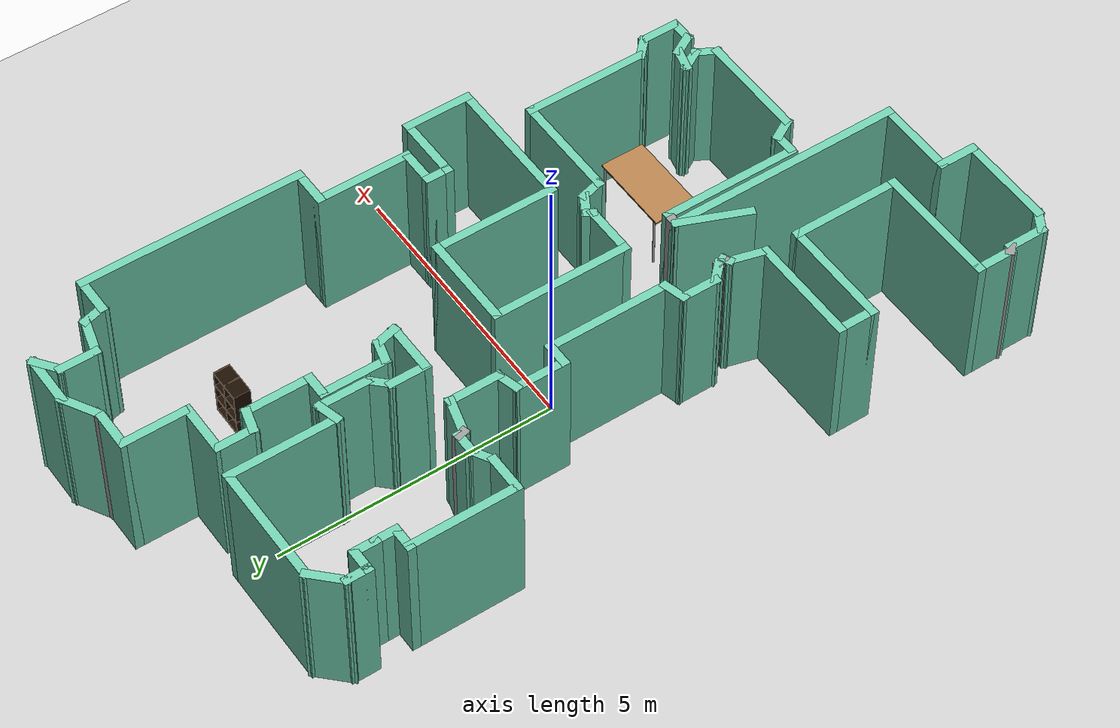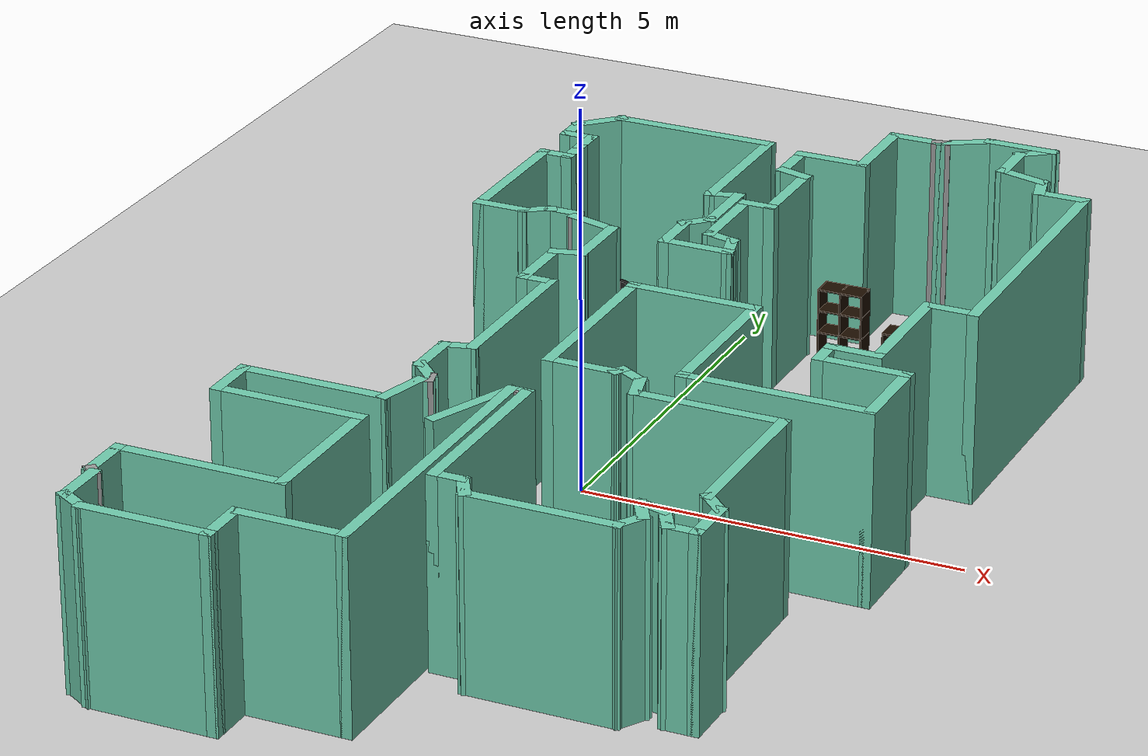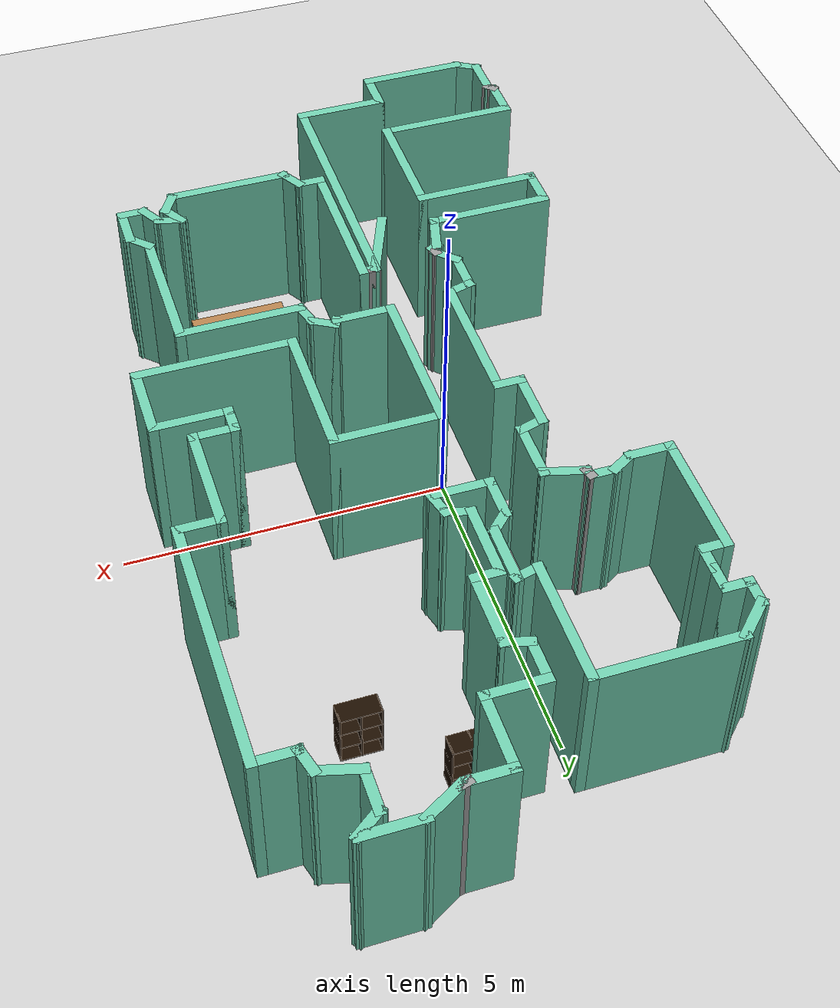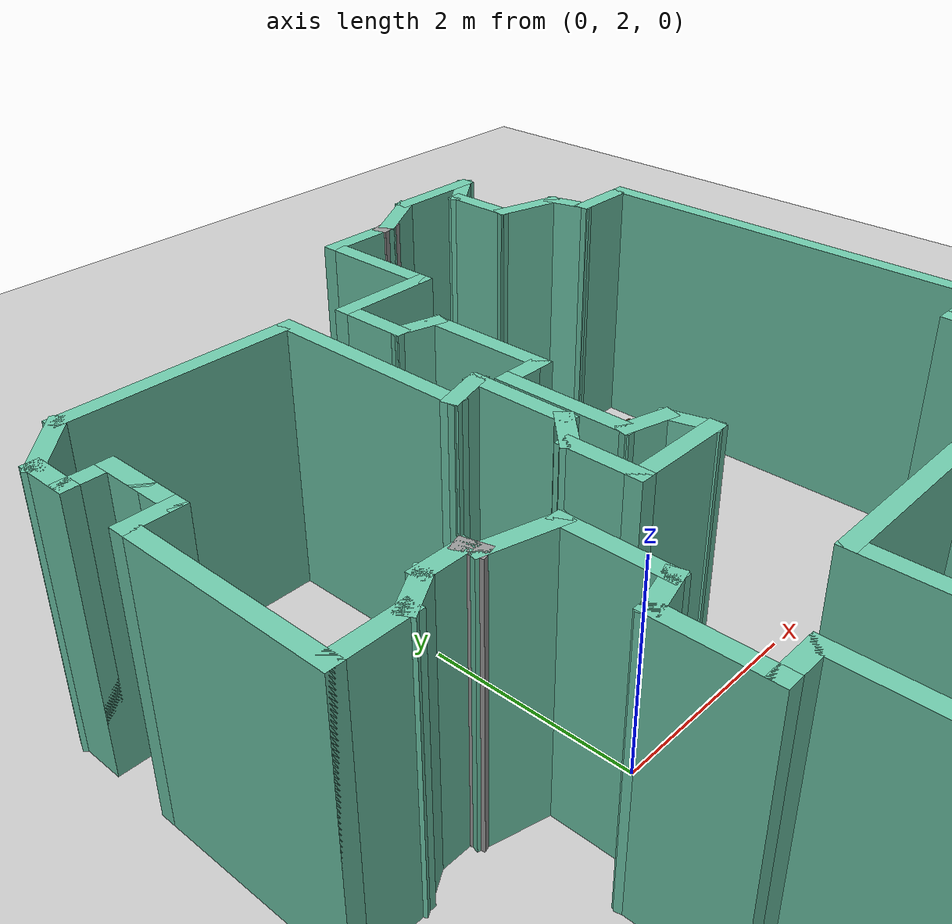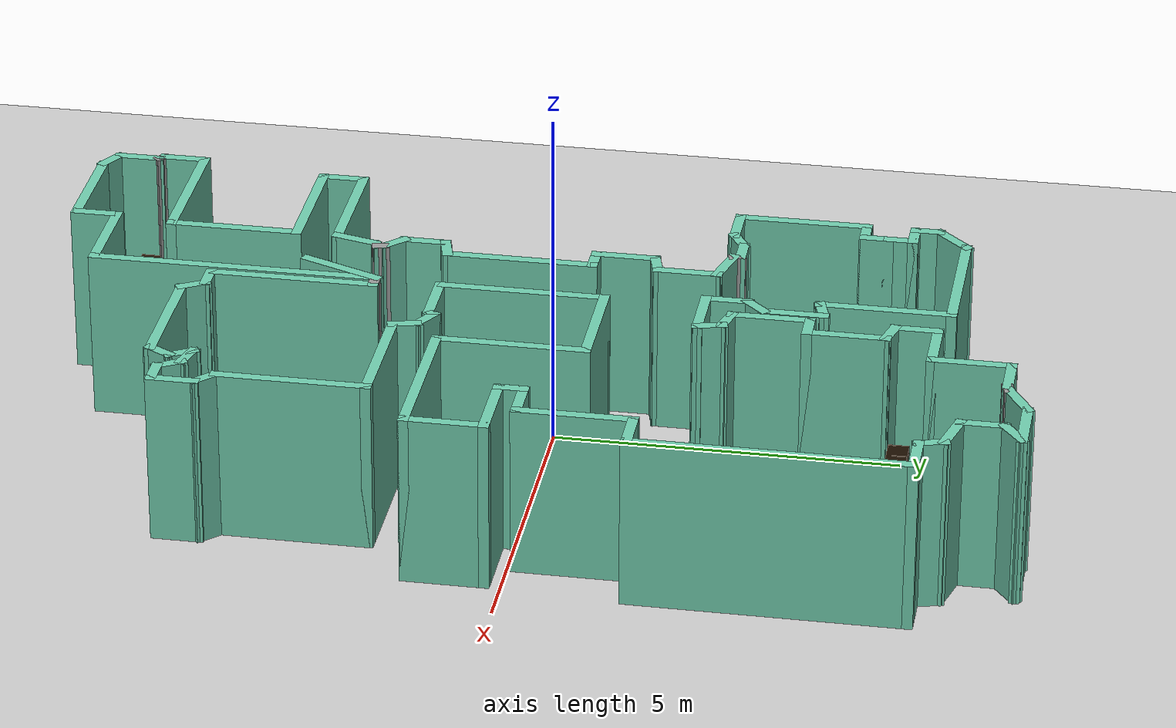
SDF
<sdf version="1.6">
 <world name="default">
  <light name="sun" type="directional">
   <pose>0 0 10 0 -0 0</pose>
   <diffuse>0.8 0.8 0.8 1</diffuse>
   <specular>0.2 0.2 0.2 1</specular>
   <attenuation>
    <range>1000</range>
    <constant>0.9</constant>
    <linear>0.01</linear>
    <quadratic>0.001</quadratic>
   </attenuation>
   <direction>-0.5 0.1 -0.9</direction>
  </light>
  <model name="ground_plane">
   <static>1</static>
   <link name="link">
    <collision name="collision">
     <geometry><plane><normal>0 0 1</normal><size>100 100</size></plane></geometry>
     <surface>
      <contact><collide_bitmask>65535</collide_bitmask></contact>
      <friction><ode><mu>100</mu><mu2>50</mu2></ode></friction>
     </surface>
    </collision>
    <visual name="visual">
     <cast_shadows>0</cast_shadows>
     <geometry><plane><normal>0 0 1</normal><size>100 100</size></plane></geometry>
     <material>
      <script><uri>file://media/materials/scripts/gazebo.material</uri><name>Gazebo/Grey</name></script>
     </material>
    </visual>
   </link>
  </model>
  <gravity>0 0 -9.8</gravity>
  <magnetic_field>6e-06 2.3e-05 -4.2e-05</magnetic_field>
  <atmosphere type="adiabatic"/>
  <physics name="default_physics" default="0" type="ode">
   <max_step_size>0.001</max_step_size>
   <real_time_factor>1</real_time_factor>
   <real_time_update_rate>1000</real_time_update_rate>
  </physics>
  <scene><ambient>0.4 0.4 0.4 1</ambient><background>0.7 0.7 0.7 1</background><shadows>1</shadows></scene>
  <audio><device>default</device></audio>
  <spherical_coordinates>
   <surface_model>EARTH_WGS84</surface_model>
   <latitude_deg>0</latitude_deg>
   <longitude_deg>0</longitude_deg>
   <elevation>0</elevation>
   <heading_deg>0</heading_deg>
  </spherical_coordinates>
  <model name="map_7">
   <pose>0.65828 -0.13295 0 0 -0 0</pose>
   <link name="Wall_0">
    <collision name="Wall_0_Collision">
     <geometry><box><size>1 0.15 2.5</size></box></geometry>
     <pose>0 0 1.25 0 -0 0</pose>
    </collision>
    <visual name="Wall_0_Visual">
     <pose>0 0 1.25 0 -0 0</pose>
     <geometry><box><size>1 0.15 2.5</size></box></geometry>
     <material>
      <script><uri>file://media/materials/scripts/gazebo.material</uri><name>Gazebo/Grey</name></script>
      <ambient>0.435294 0.796078 0.67451 1</ambient>
     </material>
     <meta><layer>0</layer></meta>
    </visual>
    <pose>2.38063 7.06866 0 0 -0 3.14159</pose>
   </link>
   <link name="Wall_1">
    <collision name="Wall_1_Collision">
     <geometry><box><size>0.75 0.15 2.5</size></box></geometry>
     <pose>0 0 1.25 0 -0 0</pose>
    </collision>
    <visual name="Wall_1_Visual">
     <pose>0 0 1.25 0 -0 0</pose>
     <geometry><box><size>0.75 0.15 2.5</size></box></geometry>
     <material>
      <script><uri>file://media/materials/scripts/gazebo.material</uri><name>Gazebo/Grey</name></script>
      <ambient>0.435294 0.796078 0.67451 1</ambient>
     </material>
     <meta><layer>0</layer></meta>
    </visual>
    <pose>1.69582 6.91866 0 0 -0 -2.61799</pose>
   </link>
   <link name="Wall_10">
    <collision name="Wall_10_Collision">
     <geometry><box><size>1.25 0.15 2.5</size></box></geometry>
     <pose>0 0 1.25 0 -0 0</pose>
    </collision>
    <visual name="Wall_10_Visual">
     <pose>0 0 1.25 0 -0 0</pose>
     <geometry><box><size>1.25 0.15 2.5</size></box></geometry>
     <material>
      <script><uri>file://media/materials/scripts/gazebo.material</uri><name>Gazebo/Grey</name></script>
      <ambient>0.435294 0.796078 0.67451 1</ambient>
     </material>
     <meta><layer>0</layer></meta>
    </visual>
    <pose>0.73942 6.19278 0 0 -0 -1.5708</pose>
   </link>
   <link name="Wall_100">
    <collision name="Wall_100_Collision">
     <geometry><box><size>0.5 0.15 2.5</size></box></geometry>
     <pose>0 0 1.25 0 -0 0</pose>
    </collision>
    <visual name="Wall_100_Visual">
     <pose>0 0 1.25 0 -0 0</pose>
     <geometry><box><size>0.5 0.15 2.5</size></box></geometry>
     <material>
      <script><uri>file://media/materials/scripts/gazebo.material</uri><name>Gazebo/Grey</name></script>
      <ambient>0.435294 0.796078 0.67451 1</ambient>
     </material>
     <meta><layer>0</layer></meta>
    </visual>
    <pose>0.92429 -1.69529 0 0 -0 1.8326</pose>
   </link>
   <link name="Wall_101">
    <collision name="Wall_101_Collision">
     <geometry><box><size>0.5 0.15 2.5</size></box></geometry>
     <pose>0 0 1.25 0 -0 0</pose>
    </collision>
    <visual name="Wall_101_Visual">
     <pose>0 0 1.25 0 -0 0</pose>
     <geometry><box><size>0.5 0.15 2.5</size></box></geometry>
     <material>
      <script><uri>file://media/materials/scripts/gazebo.material</uri><name>Gazebo/Grey</name></script>
      <ambient>0.435294 0.796078 0.67451 1</ambient>
     </material>
     <meta><layer>0</layer></meta>
    </visual>
    <pose>0.727443 -1.43876 0 0 -0 2.61799</pose>
   </link>
   <link name="Wall_102">
    <collision name="Wall_102_Collision">
     <geometry><box><size>0.25 0.15 2.5</size></box></geometry>
     <pose>0 0 1.25 0 -0 0</pose>
    </collision>
    <visual name="Wall_102_Visual">
     <pose>0 0 1.25 0 -0 0</pose>
     <geometry><box><size>0.25 0.15 2.5</size></box></geometry>
     <material>
      <script><uri>file://media/materials/scripts/gazebo.material</uri><name>Gazebo/Grey</name></script>
      <ambient>0.435294 0.796078 0.67451 1</ambient>
     </material>
     <meta><layer>0</layer></meta>
    </visual>
    <pose>0.550888 -1.39456 0 0 -0 -2.0944</pose>
   </link>
   <link name="Wall_103">
    <collision name="Wall_103_Collision">
     <geometry><box><size>1 0.15 2.5</size></box></geometry>
     <pose>0 0 1.25 0 -0 0</pose>
    </collision>
    <visual name="Wall_103_Visual">
     <pose>0 0 1.25 0 -0 0</pose>
     <geometry><box><size>1 0.15 2.5</size></box></geometry>
     <material>
      <script><uri>file://media/materials/scripts/gazebo.material</uri><name>Gazebo/Grey</name></script>
      <ambient>0.435294 0.796078 0.67451 1</ambient>
     </material>
     <meta><layer>0</layer></meta>
    </visual>
    <pose>0.100888 -1.43786 0 0 -0 3.14159</pose>
   </link>
   <link name="Wall_104">
    <collision name="Wall_104_Collision">
     <geometry><box><size>2.5 0.15 2.5</size></box></geometry>
     <pose>0 0 1.25 0 -0 0</pose>
    </collision>
    <visual name="Wall_104_Visual">
     <pose>0 0 1.25 0 -0 0</pose>
     <geometry><box><size>2.5 0.15 2.5</size></box></geometry>
     <material>
      <script><uri>file://media/materials/scripts/gazebo.material</uri><name>Gazebo/Grey</name></script>
      <ambient>0.435294 0.796078 0.67451 1</ambient>
     </material>
     <meta><layer>0</layer></meta>
    </visual>
    <pose>-0.324112 -0.26286 0 0 -0 1.5708</pose>
   </link>
   <link name="Wall_105">
    <collision name="Wall_105_Collision">
     <geometry><box><size>1.75 0.15 2.5</size></box></geometry>
     <pose>0 0 1.25 0 -0 0</pose>
    </collision>
    <visual name="Wall_105_Visual">
     <pose>0 0 1.25 0 -0 0</pose>
     <geometry><box><size>1.75 0.15 2.5</size></box></geometry>
     <material>
      <script><uri>file://media/materials/scripts/gazebo.material</uri><name>Gazebo/Grey</name></script>
      <ambient>0.435294 0.796078 0.67451 1</ambient>
     </material>
     <meta><layer>0</layer></meta>
    </visual>
    <pose>0.475888 0.91214 0 0 -0 0</pose>
   </link>
   <link name="Wall_106">
    <collision name="Wall_106_Collision">
     <geometry><box><size>2.25 0.15 2.5</size></box></geometry>
     <pose>0 0 1.25 0 -0 0</pose>
    </collision>
    <visual name="Wall_106_Visual">
     <pose>0 0 1.25 0 -0 0</pose>
     <geometry><box><size>2.25 0.15 2.5</size></box></geometry>
     <material>
      <script><uri>file://media/materials/scripts/gazebo.material</uri><name>Gazebo/Grey</name></script>
      <ambient>0.435294 0.796078 0.67451 1</ambient>
     </material>
     <meta><layer>0</layer></meta>
    </visual>
    <pose>1.27589 -0.13786 0 0 -0 -1.5708</pose>
   </link>
   <link name="Wall_107">
    <collision name="Wall_107_Collision">
     <geometry><box><size>2.5 0.15 2.5</size></box></geometry>
     <pose>0 0 1.25 0 -0 0</pose>
    </collision>
    <visual name="Wall_107_Visual">
     <pose>0 0 1.25 0 -0 0</pose>
     <geometry><box><size>2.5 0.15 2.5</size></box></geometry>
     <material>
      <script><uri>file://media/materials/scripts/gazebo.material</uri><name>Gazebo/Grey</name></script>
      <ambient>0.435294 0.796078 0.67451 1</ambient>
     </material>
     <meta><layer>0</layer></meta>
    </visual>
    <pose>2.45089 -1.18786 0 0 -0 0</pose>
   </link>
   <link name="Wall_108">
    <collision name="Wall_108_Collision">
     <geometry><box><size>1.25 0.15 2.5</size></box></geometry>
     <pose>0 0 1.25 0 -0 0</pose>
    </collision>
    <visual name="Wall_108_Visual">
     <pose>0 0 1.25 0 -0 0</pose>
     <geometry><box><size>1.25 0.15 2.5</size></box></geometry>
     <material>
      <script><uri>file://media/materials/scripts/gazebo.material</uri><name>Gazebo/Grey</name></script>
      <ambient>0.435294 0.796078 0.67451 1</ambient>
     </material>
     <meta><layer>0</layer></meta>
    </visual>
    <pose>3.62589 -0.63786 0 0 -0 1.5708</pose>
   </link>
   <link name="Wall_109">
    <collision name="Wall_109_Collision">
     <geometry><box><size>1.25 0.15 2.5</size></box></geometry>
     <pose>0 0 1.25 0 -0 0</pose>
    </collision>
    <visual name="Wall_109_Visual">
     <pose>0 0 1.25 0 -0 0</pose>
     <geometry><box><size>1.25 0.15 2.5</size></box></geometry>
     <material>
      <script><uri>file://media/materials/scripts/gazebo.material</uri><name>Gazebo/Grey</name></script>
      <ambient>0.435294 0.796078 0.67451 1</ambient>
     </material>
     <meta><layer>0</layer></meta>
    </visual>
    <pose>3.07589 -0.08786 0 0 -0 3.14159</pose>
   </link>
   <link name="Wall_11">
    <collision name="Wall_11_Collision">
     <geometry><box><size>1 0.15 2.5</size></box></geometry>
     <pose>0 0 1.25 0 -0 0</pose>
    </collision>
    <visual name="Wall_11_Visual">
     <pose>0 0 1.25 0 -0 0</pose>
     <geometry><box><size>1 0.15 2.5</size></box></geometry>
     <material>
      <script><uri>file://media/materials/scripts/gazebo.material</uri><name>Gazebo/Grey</name></script>
      <ambient>0.435294 0.796078 0.67451 1</ambient>
     </material>
     <meta><layer>0</layer></meta>
    </visual>
    <pose>0.31442 5.64278 0 0 -0 3.14159</pose>
   </link>
   <link name="Wall_110">
    <collision name="Wall_110_Collision">
     <geometry><box><size>0.5 0.15 2.5</size></box></geometry>
     <pose>0 0 1.25 0 -0 0</pose>
    </collision>
    <visual name="Wall_110_Visual">
     <pose>0 0 1.25 0 -0 0</pose>
     <geometry><box><size>0.5 0.15 2.5</size></box></geometry>
     <material>
      <script><uri>file://media/materials/scripts/gazebo.material</uri><name>Gazebo/Grey</name></script>
      <ambient>0.435294 0.796078 0.67451 1</ambient>
     </material>
     <meta><layer>0</layer></meta>
    </visual>
    <pose>2.52589 0.08714 0 0 -0 1.5708</pose>
   </link>
   <link name="Wall_111">
    <collision name="Wall_111_Collision">
     <geometry><box><size>0.75 0.15 2.5</size></box></geometry>
     <pose>0 0 1.25 0 -0 0</pose>
    </collision>
    <visual name="Wall_111_Visual">
     <pose>0 0 1.25 0 -0 0</pose>
     <geometry><box><size>0.75 0.15 2.5</size></box></geometry>
     <material>
      <script><uri>file://media/materials/scripts/gazebo.material</uri><name>Gazebo/Grey</name></script>
      <ambient>0.435294 0.796078 0.67451 1</ambient>
     </material>
     <meta><layer>0</layer></meta>
    </visual>
    <pose>2.82589 0.26214 0 0 -0 0</pose>
   </link>
   <link name="Wall_112">
    <collision name="Wall_112_Collision">
     <geometry><box><size>1.75 0.15 2.5</size></box></geometry>
     <pose>0 0 1.25 0 -0 0</pose>
    </collision>
    <visual name="Wall_112_Visual">
     <pose>0 0 1.25 0 -0 0</pose>
     <geometry><box><size>1.75 0.15 2.5</size></box></geometry>
     <material>
      <script><uri>file://media/materials/scripts/gazebo.material</uri><name>Gazebo/Grey</name></script>
      <ambient>0.435294 0.796078 0.67451 1</ambient>
     </material>
     <meta><layer>0</layer></meta>
    </visual>
    <pose>3.12589 1.06214 0 0 -0 1.5708</pose>
   </link>
   <link name="Wall_115">
    <collision name="Wall_115_Collision">
     <geometry><box><size>0.75 0.15 2.5</size></box></geometry>
     <pose>0 0 1.25 0 -0 0</pose>
    </collision>
    <visual name="Wall_115_Visual">
     <pose>0 0 1.25 0 -0 0</pose>
     <geometry><box><size>0.75 0.15 2.5</size></box></geometry>
     <material>
      <script><uri>file://media/materials/scripts/gazebo.material</uri><name>Gazebo/Grey</name></script>
      <ambient>0.435294 0.796078 0.67451 1</ambient>
     </material>
     <meta><layer>0</layer></meta>
    </visual>
    <pose>3.42589 1.86214 0 0 -0 0</pose>
   </link>
   <link name="Wall_116">
    <collision name="Wall_116_Collision">
     <geometry><box><size>4 0.15 2.5</size></box></geometry>
     <pose>0 0 1.25 0 -0 0</pose>
    </collision>
    <visual name="Wall_116_Visual">
     <pose>0 0 1.25 0 -0 0</pose>
     <geometry><box><size>4 0.15 2.5</size></box></geometry>
     <material>
      <script><uri>file://media/materials/scripts/gazebo.material</uri><name>Gazebo/Grey</name></script>
      <ambient>0.435294 0.796078 0.67451 1</ambient>
     </material>
     <meta><layer>0</layer></meta>
    </visual>
    <pose>3.72589 3.78714 0 0 -0 1.5708</pose>
   </link>
   <link name="Wall_117">
    <collision name="Wall_117_Collision">
     <geometry><box><size>0.75 0.15 2.5</size></box></geometry>
     <pose>0 0 1.25 0 -0 0</pose>
    </collision>
    <visual name="Wall_117_Visual">
     <pose>0 0 1.25 0 -0 0</pose>
     <geometry><box><size>0.75 0.15 2.5</size></box></geometry>
     <material>
      <script><uri>file://media/materials/scripts/gazebo.material</uri><name>Gazebo/Grey</name></script>
      <ambient>0.435294 0.796078 0.67451 1</ambient>
     </material>
     <meta><layer>0</layer></meta>
    </visual>
    <pose>3.42589 5.71214 0 0 -0 3.14159</pose>
   </link>
   <link name="Wall_118">
    <collision name="Wall_118_Collision">
     <geometry><box><size>0.5 0.15 2.5</size></box></geometry>
     <pose>0 0 1.25 0 -0 0</pose>
    </collision>
    <visual name="Wall_118_Visual">
     <pose>0 0 1.25 0 -0 0</pose>
     <geometry><box><size>0.5 0.15 2.5</size></box></geometry>
     <material>
      <script><uri>file://media/materials/scripts/gazebo.material</uri><name>Gazebo/Grey</name></script>
      <ambient>0.435294 0.796078 0.67451 1</ambient>
     </material>
     <meta><layer>0</layer></meta>
    </visual>
    <pose>3.0806 5.88118 0 0 -0 1.8326</pose>
   </link>
   <link name="Wall_119">
    <collision name="Wall_119_Collision">
     <geometry><box><size>0.75 0.15 2.5</size></box></geometry>
     <pose>0 0 1.25 0 -0 0</pose>
    </collision>
    <visual name="Wall_119_Visual">
     <pose>0 0 1.25 0 -0 0</pose>
     <geometry><box><size>0.75 0.15 2.5</size></box></geometry>
     <material>
      <script><uri>file://media/materials/scripts/gazebo.material</uri><name>Gazebo/Grey</name></script>
      <ambient>0.435294 0.796078 0.67451 1</ambient>
     </material>
     <meta><layer>0</layer></meta>
    </visual>
    <pose>2.74552 6.12786 0 0 -0 2.87979</pose>
   </link>
   <link name="Wall_122">
    <collision name="Wall_122_Collision">
     <geometry><box><size>0.75 0.15 2.5</size></box></geometry>
     <pose>0 0 1.25 0 -0 0</pose>
    </collision>
    <visual name="Wall_122_Visual">
     <pose>0 0 1.25 0 -0 0</pose>
     <geometry><box><size>0.75 0.15 2.5</size></box></geometry>
     <material>
      <script><uri>file://media/materials/scripts/gazebo.material</uri><name>Gazebo/Grey</name></script>
      <ambient>0.435294 0.796078 0.67451 1</ambient>
     </material>
     <meta><layer>0</layer></meta>
    </visual>
    <pose>2.45575 6.50551 0 0 -0 1.5708</pose>
   </link>
   <link name="Wall_123">
    <collision name="Wall_123_Collision">
     <geometry><box><size>0.587801 0.15 2.5</size></box></geometry>
     <pose>0 0 1.25 0 -0 0</pose>
    </collision>
    <visual name="Wall_123_Visual">
     <pose>0 0 1.25 0 -0 0</pose>
     <geometry><box><size>0.587801 0.15 2.5</size></box></geometry>
     <material>
      <script><uri>file://media/materials/scripts/gazebo.material</uri><name>Gazebo/Grey</name></script>
      <ambient>0.435294 0.796078 0.67451 1</ambient>
     </material>
     <meta><layer>0</layer></meta>
    </visual>
    <pose>2.63069 6.93708 0 0 -0 0.644866</pose>
   </link>
   <link name="Wall_125">
    <collision name="Wall_125_Collision">
     <geometry><box><size>1.32079 0.15 2.5</size></box></geometry>
     <pose>0 0 1.25 0 -0 0</pose>
    </collision>
    <visual name="Wall_125_Visual">
     <pose>0 0 1.25 0 -0 0</pose>
     <geometry><box><size>1.32079 0.15 2.5</size></box></geometry>
     <material>
      <script><uri>file://media/materials/scripts/gazebo.material</uri><name>Gazebo/Grey</name></script>
      <ambient>0.435294 0.796078 0.67451 1</ambient>
     </material>
     <meta><layer>0</layer></meta>
    </visual>
    <pose>-0.594171 -2.91242 0 0 -0 1.17967</pose>
   </link>
   <link name="Wall_16">
    <collision name="Wall_16_Collision">
     <geometry><box><size>0.75 0.15 2.5</size></box></geometry>
     <pose>0 0 1.25 0 -0 0</pose>
    </collision>
    <visual name="Wall_16_Visual">
     <pose>0 0 1.25 0 -0 0</pose>
     <geometry><box><size>0.75 0.15 2.5</size></box></geometry>
     <material>
      <script><uri>file://media/materials/scripts/gazebo.material</uri><name>Gazebo/Grey</name></script>
      <ambient>0.435294 0.796078 0.67451 1</ambient>
     </material>
     <meta><layer>0</layer></meta>
    </visual>
    <pose>-0.11058 5.34278 0 0 -0 -1.5708</pose>
   </link>
   <link name="Wall_17">
    <collision name="Wall_17_Collision">
     <geometry><box><size>0.5 0.15 2.5</size></box></geometry>
     <pose>0 0 1.25 0 -0 0</pose>
    </collision>
    <visual name="Wall_17_Visual">
     <pose>0 0 1.25 0 -0 0</pose>
     <geometry><box><size>0.5 0.15 2.5</size></box></geometry>
     <material>
      <script><uri>file://media/materials/scripts/gazebo.material</uri><name>Gazebo/Grey</name></script>
      <ambient>0.435294 0.796078 0.67451 1</ambient>
     </material>
     <meta><layer>0</layer></meta>
    </visual>
    <pose>0.058457 4.99749 0 0 -0 -0.261799</pose>
   </link>
   <link name="Wall_18">
    <collision name="Wall_18_Collision">
     <geometry><box><size>1.25 0.15 2.5</size></box></geometry>
     <pose>0 0 1.25 0 -0 0</pose>
    </collision>
    <visual name="Wall_18_Visual">
     <pose>0 0 1.25 0 -0 0</pose>
     <geometry><box><size>1.25 0.15 2.5</size></box></geometry>
     <material>
      <script><uri>file://media/materials/scripts/gazebo.material</uri><name>Gazebo/Grey</name></script>
      <ambient>0.435294 0.796078 0.67451 1</ambient>
     </material>
     <meta><layer>0</layer></meta>
    </visual>
    <pose>0.227494 4.40219 0 0 -0 -1.5708</pose>
   </link>
   <link name="Wall_19">
    <collision name="Wall_19_Collision">
     <geometry><box><size>0.5 0.15 2.5</size></box></geometry>
     <pose>0 0 1.25 0 -0 0</pose>
    </collision>
    <visual name="Wall_19_Visual">
     <pose>0 0 1.25 0 -0 0</pose>
     <geometry><box><size>0.5 0.15 2.5</size></box></geometry>
     <material>
      <script><uri>file://media/materials/scripts/gazebo.material</uri><name>Gazebo/Grey</name></script>
      <ambient>0.435294 0.796078 0.67451 1</ambient>
     </material>
     <meta><layer>0</layer></meta>
    </visual>
    <pose>0.052494 3.8522 0 0 -0 3.14159</pose>
   </link>
   <link name="Wall_20">
    <collision name="Wall_20_Collision">
     <geometry><box><size>1.25 0.15 2.5</size></box></geometry>
     <pose>0 0 1.25 0 -0 0</pose>
    </collision>
    <visual name="Wall_20_Visual">
     <pose>0 0 1.25 0 -0 0</pose>
     <geometry><box><size>1.25 0.15 2.5</size></box></geometry>
     <material>
      <script><uri>file://media/materials/scripts/gazebo.material</uri><name>Gazebo/Grey</name></script>
      <ambient>0.435294 0.796078 0.67451 1</ambient>
     </material>
     <meta><layer>0</layer></meta>
    </visual>
    <pose>-0.122506 3.3022 0 0 -0 -1.5708</pose>
   </link>
   <link name="Wall_21">
    <collision name="Wall_21_Collision">
     <geometry><box><size>0.5 0.15 2.5</size></box></geometry>
     <pose>0 0 1.25 0 -0 0</pose>
    </collision>
    <visual name="Wall_21_Visual">
     <pose>0 0 1.25 0 -0 0</pose>
     <geometry><box><size>0.5 0.15 2.5</size></box></geometry>
     <material>
      <script><uri>file://media/materials/scripts/gazebo.material</uri><name>Gazebo/Grey</name></script>
      <ambient>0.435294 0.796078 0.67451 1</ambient>
     </material>
     <meta><layer>0</layer></meta>
    </visual>
    <pose>0.046531 2.7069 0 0 -0 -0.261799</pose>
   </link>
   <link name="Wall_22">
    <collision name="Wall_22_Collision">
     <geometry><box><size>0.5 0.15 2.5</size></box></geometry>
     <pose>0 0 1.25 0 -0 0</pose>
    </collision>
    <visual name="Wall_22_Visual">
     <pose>0 0 1.25 0 -0 0</pose>
     <geometry><box><size>0.5 0.15 2.5</size></box></geometry>
     <material>
      <script><uri>file://media/materials/scripts/gazebo.material</uri><name>Gazebo/Grey</name></script>
      <ambient>0.435294 0.796078 0.67451 1</ambient>
     </material>
     <meta><layer>0</layer></meta>
    </visual>
    <pose>0.260861 2.49257 0 0 -0 -1.309</pose>
   </link>
   <link name="Wall_25">
    <collision name="Wall_25_Collision">
     <geometry><box><size>1 0.15 2.5</size></box></geometry>
     <pose>0 0 1.25 0 -0 0</pose>
    </collision>
    <visual name="Wall_25_Visual">
     <pose>0 0 1.25 0 -0 0</pose>
     <geometry><box><size>1 0.15 2.5</size></box></geometry>
     <material>
      <script><uri>file://media/materials/scripts/gazebo.material</uri><name>Gazebo/Grey</name></script>
      <ambient>0.435294 0.796078 0.67451 1</ambient>
     </material>
     <meta><layer>0</layer></meta>
    </visual>
    <pose>-0.118845 2.32353 0 0 -0 3.14159</pose>
   </link>
   <link name="Wall_26">
    <collision name="Wall_26_Collision">
     <geometry><box><size>0.75 0.15 2.5</size></box></geometry>
     <pose>0 0 1.25 0 -0 0</pose>
    </collision>
    <visual name="Wall_26_Visual">
     <pose>0 0 1.25 0 -0 0</pose>
     <geometry><box><size>0.75 0.15 2.5</size></box></geometry>
     <material>
      <script><uri>file://media/materials/scripts/gazebo.material</uri><name>Gazebo/Grey</name></script>
      <ambient>0.435294 0.796078 0.67451 1</ambient>
     </material>
     <meta><layer>0</layer></meta>
    </visual>
    <pose>-0.543845 2.62353 0 0 -0 1.5708</pose>
   </link>
   <link name="Wall_29">
    <collision name="Wall_29_Collision">
     <geometry><box><size>0.5 0.15 2.5</size></box></geometry>
     <pose>0 0 1.25 0 -0 0</pose>
    </collision>
    <visual name="Wall_29_Visual">
     <pose>0 0 1.25 0 -0 0</pose>
     <geometry><box><size>0.5 0.15 2.5</size></box></geometry>
     <material>
      <script><uri>file://media/materials/scripts/gazebo.material</uri><name>Gazebo/Grey</name></script>
      <ambient>0.435294 0.796078 0.67451 1</ambient>
     </material>
     <meta><layer>0</layer></meta>
    </visual>
    <pose>-0.420102 3.04728 0 0 -0 0.785398</pose>
   </link>
   <link name="Wall_30">
    <collision name="Wall_30_Collision">
     <geometry><box><size>1 0.15 2.5</size></box></geometry>
     <pose>0 0 1.25 0 -0 0</pose>
    </collision>
    <visual name="Wall_30_Visual">
     <pose>0 0 1.25 0 -0 0</pose>
     <geometry><box><size>1 0.15 2.5</size></box></geometry>
     <material>
      <script><uri>file://media/materials/scripts/gazebo.material</uri><name>Gazebo/Grey</name></script>
      <ambient>0.435294 0.796078 0.67451 1</ambient>
     </material>
     <meta><layer>0</layer></meta>
    </visual>
    <pose>-0.296358 3.59602 0 0 -0 1.5708</pose>
   </link>
   <link name="Wall_31">
    <collision name="Wall_31_Collision">
     <geometry><box><size>0.5 0.15 2.5</size></box></geometry>
     <pose>0 0 1.25 0 -0 0</pose>
    </collision>
    <visual name="Wall_31_Visual">
     <pose>0 0 1.25 0 -0 0</pose>
     <geometry><box><size>0.5 0.15 2.5</size></box></geometry>
     <material>
      <script><uri>file://media/materials/scripts/gazebo.material</uri><name>Gazebo/Grey</name></script>
      <ambient>0.435294 0.796078 0.67451 1</ambient>
     </material>
     <meta><layer>0</layer></meta>
    </visual>
    <pose>-0.465395 3.97573 0 0 -0 -2.87979</pose>
   </link>
   <link name="Wall_32">
    <collision name="Wall_32_Collision">
     <geometry><box><size>2 0.15 2.5</size></box></geometry>
     <pose>0 0 1.25 0 -0 0</pose>
    </collision>
    <visual name="Wall_32_Visual">
     <pose>0 0 1.25 0 -0 0</pose>
     <geometry><box><size>2 0.15 2.5</size></box></geometry>
     <material>
      <script><uri>file://media/materials/scripts/gazebo.material</uri><name>Gazebo/Grey</name></script>
      <ambient>0.435294 0.796078 0.67451 1</ambient>
     </material>
     <meta><layer>0</layer></meta>
    </visual>
    <pose>-0.634432 4.85543 0 0 -0 1.5708</pose>
   </link>
   <link name="Wall_33">
    <collision name="Wall_33_Collision">
     <geometry><box><size>2.25 0.15 2.5</size></box></geometry>
     <pose>0 0 1.25 0 -0 0</pose>
    </collision>
    <visual name="Wall_33_Visual">
     <pose>0 0 1.25 0 -0 0</pose>
     <geometry><box><size>2.25 0.15 2.5</size></box></geometry>
     <material>
      <script><uri>file://media/materials/scripts/gazebo.material</uri><name>Gazebo/Grey</name></script>
      <ambient>0.435294 0.796078 0.67451 1</ambient>
     </material>
     <meta><layer>0</layer></meta>
    </visual>
    <pose>-1.68443 5.78043 0 0 -0 3.14159</pose>
   </link>
   <link name="Wall_34">
    <collision name="Wall_34_Collision">
     <geometry><box><size>0.75 0.15 2.5</size></box></geometry>
     <pose>0 0 1.25 0 -0 0</pose>
    </collision>
    <visual name="Wall_34_Visual">
     <pose>0 0 1.25 0 -0 0</pose>
     <geometry><box><size>0.75 0.15 2.5</size></box></geometry>
     <material>
      <script><uri>file://media/materials/scripts/gazebo.material</uri><name>Gazebo/Grey</name></script>
      <ambient>0.435294 0.796078 0.67451 1</ambient>
     </material>
     <meta><layer>0</layer></meta>
    </visual>
    <pose>-2.94656 5.5683 0 0 -0 -2.35619</pose>
   </link>
   <link name="Wall_35">
    <collision name="Wall_35_Collision">
     <geometry><box><size>0.5 0.15 2.5</size></box></geometry>
     <pose>0 0 1.25 0 -0 0</pose>
    </collision>
    <visual name="Wall_35_Visual">
     <pose>0 0 1.25 0 -0 0</pose>
     <geometry><box><size>0.5 0.15 2.5</size></box></geometry>
     <material>
      <script><uri>file://media/materials/scripts/gazebo.material</uri><name>Gazebo/Grey</name></script>
      <ambient>0.435294 0.796078 0.67451 1</ambient>
     </material>
     <meta><layer>0</layer></meta>
    </visual>
    <pose>-3.1587 5.18117 0 0 -0 -1.5708</pose>
   </link>
   <link name="Wall_36">
    <collision name="Wall_36_Collision">
     <geometry><box><size>0.5 0.15 2.5</size></box></geometry>
     <pose>0 0 1.25 0 -0 0</pose>
    </collision>
    <visual name="Wall_36_Visual">
     <pose>0 0 1.25 0 -0 0</pose>
     <geometry><box><size>0.5 0.15 2.5</size></box></geometry>
     <material>
      <script><uri>file://media/materials/scripts/gazebo.material</uri><name>Gazebo/Grey</name></script>
      <ambient>0.435294 0.796078 0.67451 1</ambient>
     </material>
     <meta><layer>0</layer></meta>
    </visual>
    <pose>-2.9837 5.00617 0 0 -0 0</pose>
   </link>
   <link name="Wall_37">
    <collision name="Wall_37_Collision">
     <geometry><box><size>0.5 0.15 2.5</size></box></geometry>
     <pose>0 0 1.25 0 -0 0</pose>
    </collision>
    <visual name="Wall_37_Visual">
     <pose>0 0 1.25 0 -0 0</pose>
     <geometry><box><size>0.5 0.15 2.5</size></box></geometry>
     <material>
      <script><uri>file://media/materials/scripts/gazebo.material</uri><name>Gazebo/Grey</name></script>
      <ambient>0.435294 0.796078 0.67451 1</ambient>
     </material>
     <meta><layer>0</layer></meta>
    </visual>
    <pose>-2.8087 4.83117 0 0 -0 -1.5708</pose>
   </link>
   <link name="Wall_38">
    <collision name="Wall_38_Collision">
     <geometry><box><size>0.5 0.15 2.5</size></box></geometry>
     <pose>0 0 1.25 0 -0 0</pose>
    </collision>
    <visual name="Wall_38_Visual">
     <pose>0 0 1.25 0 -0 0</pose>
     <geometry><box><size>0.5 0.15 2.5</size></box></geometry>
     <material>
      <script><uri>file://media/materials/scripts/gazebo.material</uri><name>Gazebo/Grey</name></script>
      <ambient>0.435294 0.796078 0.67451 1</ambient>
     </material>
     <meta><layer>0</layer></meta>
    </visual>
    <pose>-2.8087 4.48117 0 0 -0 -1.5708</pose>
   </link>
   <link name="Wall_39">
    <collision name="Wall_39_Collision">
     <geometry><box><size>0.5 0.15 2.5</size></box></geometry>
     <pose>0 0 1.25 0 -0 0</pose>
    </collision>
    <visual name="Wall_39_Visual">
     <pose>0 0 1.25 0 -0 0</pose>
     <geometry><box><size>0.5 0.15 2.5</size></box></geometry>
     <material>
      <script><uri>file://media/materials/scripts/gazebo.material</uri><name>Gazebo/Grey</name></script>
      <ambient>0.435294 0.796078 0.67451 1</ambient>
     </material>
     <meta><layer>0</layer></meta>
    </visual>
    <pose>-2.9837 4.30617 0 0 -0 3.14159</pose>
   </link>
   <link name="Wall_4">
    <collision name="Wall_4_Collision">
     <geometry><box><size>0.25 0.15 2.5</size></box></geometry>
     <pose>0 0 1.25 0 -0 0</pose>
    </collision>
    <visual name="Wall_4_Visual">
     <pose>0 0 1.25 0 -0 0</pose>
     <geometry><box><size>0.25 0.15 2.5</size></box></geometry>
     <material>
      <script><uri>file://media/materials/scripts/gazebo.material</uri><name>Gazebo/Grey</name></script>
      <ambient>1 1 1 1</ambient>
     </material>
     <meta><layer>0</layer></meta>
    </visual>
    <pose>1.38772 6.75572 0 0 -0 -2.87979</pose>
   </link>
   <link name="Wall_40">
    <collision name="Wall_40_Collision">
     <geometry><box><size>2 0.15 2.5</size></box></geometry>
     <pose>0 0 1.25 0 -0 0</pose>
    </collision>
    <visual name="Wall_40_Visual">
     <pose>0 0 1.25 0 -0 0</pose>
     <geometry><box><size>2 0.15 2.5</size></box></geometry>
     <material>
      <script><uri>file://media/materials/scripts/gazebo.material</uri><name>Gazebo/Grey</name></script>
      <ambient>0.435294 0.796078 0.67451 1</ambient>
     </material>
     <meta><layer>0</layer></meta>
    </visual>
    <pose>-3.1587 3.38117 0 0 -0 -1.5708</pose>
   </link>
   <link name="Wall_41">
    <collision name="Wall_41_Collision">
     <geometry><box><size>0.75 0.15 2.5</size></box></geometry>
     <pose>0 0 1.25 0 -0 0</pose>
    </collision>
    <visual name="Wall_41_Visual">
     <pose>0 0 1.25 0 -0 0</pose>
     <geometry><box><size>0.75 0.15 2.5</size></box></geometry>
     <material>
      <script><uri>file://media/materials/scripts/gazebo.material</uri><name>Gazebo/Grey</name></script>
      <ambient>0.435294 0.796078 0.67451 1</ambient>
     </material>
     <meta><layer>0</layer></meta>
    </visual>
    <pose>-2.8587 2.45617 0 0 -0 0</pose>
   </link>
   <link name="Wall_42">
    <collision name="Wall_42_Collision">
     <geometry><box><size>0.5 0.15 2.5</size></box></geometry>
     <pose>0 0 1.25 0 -0 0</pose>
    </collision>
    <visual name="Wall_42_Visual">
     <pose>0 0 1.25 0 -0 0</pose>
     <geometry><box><size>0.5 0.15 2.5</size></box></geometry>
     <material>
      <script><uri>file://media/materials/scripts/gazebo.material</uri><name>Gazebo/Grey</name></script>
      <ambient>0.435294 0.796078 0.67451 1</ambient>
     </material>
     <meta><layer>0</layer></meta>
    </visual>
    <pose>-2.40714 2.54367 0 0 -0 0.523599</pose>
   </link>
   <link name="Wall_43">
    <collision name="Wall_43_Collision">
     <geometry><box><size>0.5 0.15 2.5</size></box></geometry>
     <pose>0 0 1.25 0 -0 0</pose>
    </collision>
    <visual name="Wall_43_Visual">
     <pose>0 0 1.25 0 -0 0</pose>
     <geometry><box><size>0.5 0.15 2.5</size></box></geometry>
     <material>
      <script><uri>file://media/materials/scripts/gazebo.material</uri><name>Gazebo/Grey</name></script>
      <ambient>0.435294 0.796078 0.67451 1</ambient>
     </material>
     <meta><layer>0</layer></meta>
    </visual>
    <pose>-2.08059 2.63117 0 0 -0 0</pose>
   </link>
   <link name="Wall_44">
    <collision name="Wall_44_Collision">
     <geometry><box><size>0.25 0.15 2.5</size></box></geometry>
     <pose>0 0 1.25 0 -0 0</pose>
    </collision>
    <visual name="Wall_44_Visual">
     <pose>0 0 1.25 0 -0 0</pose>
     <geometry><box><size>0.25 0.15 2.5</size></box></geometry>
     <material>
      <script><uri>file://media/materials/scripts/gazebo.material</uri><name>Gazebo/Grey</name></script>
      <ambient>1 1 1 1</ambient>
     </material>
     <meta><layer>0</layer></meta>
    </visual>
    <pose>-1.89265 2.58288 0 0 -0 -1.309</pose>
   </link>
   <link name="Wall_45">
    <collision name="Wall_45_Collision">
     <geometry><box><size>0.75 0.15 2.5</size></box></geometry>
     <pose>0 0 1.25 0 -0 0</pose>
    </collision>
    <visual name="Wall_45_Visual">
     <pose>0 0 1.25 0 -0 0</pose>
     <geometry><box><size>0.75 0.15 2.5</size></box></geometry>
     <material>
      <script><uri>file://media/materials/scripts/gazebo.material</uri><name>Gazebo/Grey</name></script>
      <ambient>0.435294 0.796078 0.67451 1</ambient>
     </material>
     <meta><layer>0</layer></meta>
    </visual>
    <pose>-1.58993 2.45693 0 0 -0 -0.261799</pose>
   </link>
   <link name="Wall_46">
    <collision name="Wall_46_Collision">
     <geometry><box><size>1 0.15 2.5</size></box></geometry>
     <pose>0 0 1.25 0 -0 0</pose>
    </collision>
    <visual name="Wall_46_Visual">
     <pose>0 0 1.25 0 -0 0</pose>
     <geometry><box><size>1 0.15 2.5</size></box></geometry>
     <material>
      <script><uri>file://media/materials/scripts/gazebo.material</uri><name>Gazebo/Grey</name></script>
      <ambient>0.435294 0.796078 0.67451 1</ambient>
     </material>
     <meta><layer>0</layer></meta>
    </visual>
    <pose>-1.30015 1.95429 0 0 -0 -1.5708</pose>
   </link>
   <link name="Wall_47">
    <collision name="Wall_47_Collision">
     <geometry><box><size>0.5 0.15 2.5</size></box></geometry>
     <pose>0 0 1.25 0 -0 0</pose>
    </collision>
    <visual name="Wall_47_Visual">
     <pose>0 0 1.25 0 -0 0</pose>
     <geometry><box><size>0.5 0.15 2.5</size></box></geometry>
     <material>
      <script><uri>file://media/materials/scripts/gazebo.material</uri><name>Gazebo/Grey</name></script>
      <ambient>0.435294 0.796078 0.67451 1</ambient>
     </material>
     <meta><layer>0</layer></meta>
    </visual>
    <pose>-1.46919 1.48399 0 0 -0 -2.87979</pose>
   </link>
   <link name="Wall_48">
    <collision name="Wall_48_Collision">
     <geometry><box><size>1 0.15 2.5</size></box></geometry>
     <pose>0 0 1.25 0 -0 0</pose>
    </collision>
    <visual name="Wall_48_Visual">
     <pose>0 0 1.25 0 -0 0</pose>
     <geometry><box><size>1 0.15 2.5</size></box></geometry>
     <material>
      <script><uri>file://media/materials/scripts/gazebo.material</uri><name>Gazebo/Grey</name></script>
      <ambient>0.435294 0.796078 0.67451 1</ambient>
     </material>
     <meta><layer>0</layer></meta>
    </visual>
    <pose>-1.63822 1.0137 0 0 -0 -1.5708</pose>
   </link>
   <link name="Wall_49">
    <collision name="Wall_49_Collision">
     <geometry><box><size>0.5 0.15 2.5</size></box></geometry>
     <pose>0 0 1.25 0 -0 0</pose>
    </collision>
    <visual name="Wall_49_Visual">
     <pose>0 0 1.25 0 -0 0</pose>
     <geometry><box><size>0.5 0.15 2.5</size></box></geometry>
     <material>
      <script><uri>file://media/materials/scripts/gazebo.material</uri><name>Gazebo/Grey</name></script>
      <ambient>0.435294 0.796078 0.67451 1</ambient>
     </material>
     <meta><layer>0</layer></meta>
    </visual>
    <pose>-1.46322 0.588701 0 0 -0 0</pose>
   </link>
   <link name="Wall_5">
    <collision name="Wall_5_Collision">
     <geometry><box><size>0.75 0.15 2.5</size></box></geometry>
     <pose>0 0 1.25 0 -0 0</pose>
    </collision>
    <visual name="Wall_5_Visual">
     <pose>0 0 1.25 0 -0 0</pose>
     <geometry><box><size>0.75 0.15 2.5</size></box></geometry>
     <material>
      <script><uri>file://media/materials/scripts/gazebo.material</uri><name>Gazebo/Grey</name></script>
      <ambient>0.435294 0.796078 0.67451 1</ambient>
     </material>
     <meta><layer>0</layer></meta>
    </visual>
    <pose>1.03942 6.74278 0 0 -0 3.14159</pose>
   </link>
   <link name="Wall_50">
    <collision name="Wall_50_Collision">
     <geometry><box><size>2.25 0.15 2.5</size></box></geometry>
     <pose>0 0 1.25 0 -0 0</pose>
    </collision>
    <visual name="Wall_50_Visual">
     <pose>0 0 1.25 0 -0 0</pose>
     <geometry><box><size>2.25 0.15 2.5</size></box></geometry>
     <material>
      <script><uri>file://media/materials/scripts/gazebo.material</uri><name>Gazebo/Grey</name></script>
      <ambient>0.435294 0.796078 0.67451 1</ambient>
     </material>
     <meta><layer>0</layer></meta>
    </visual>
    <pose>-1.28822 -0.4613 0 0 -0 -1.5708</pose>
   </link>
   <link name="Wall_55">
    <collision name="Wall_55_Collision">
     <geometry><box><size>0.5 0.15 2.5</size></box></geometry>
     <pose>0 0 1.25 0 -0 0</pose>
    </collision>
    <visual name="Wall_55_Visual">
     <pose>0 0 1.25 0 -0 0</pose>
     <geometry><box><size>0.5 0.15 2.5</size></box></geometry>
     <material>
      <script><uri>file://media/materials/scripts/gazebo.material</uri><name>Gazebo/Grey</name></script>
      <ambient>0.435294 0.796078 0.67451 1</ambient>
     </material>
     <meta><layer>0</layer></meta>
    </visual>
    <pose>-1.45726 -1.55659 0 0 -0 -2.87979</pose>
   </link>
   <link name="Wall_56">
    <collision name="Wall_56_Collision">
     <geometry><box><size>0.75 0.15 2.5</size></box></geometry>
     <pose>0 0 1.25 0 -0 0</pose>
    </collision>
    <visual name="Wall_56_Visual">
     <pose>0 0 1.25 0 -0 0</pose>
     <geometry><box><size>0.75 0.15 2.5</size></box></geometry>
     <material>
      <script><uri>file://media/materials/scripts/gazebo.material</uri><name>Gazebo/Grey</name></script>
      <ambient>0.435294 0.796078 0.67451 1</ambient>
     </material>
     <meta><layer>0</layer></meta>
    </visual>
    <pose>-1.6263 -1.90189 0 0 -0 -1.5708</pose>
   </link>
   <link name="Wall_57">
    <collision name="Wall_57_Collision">
     <geometry><box><size>0.5 0.15 2.5</size></box></geometry>
     <pose>0 0 1.25 0 -0 0</pose>
    </collision>
    <visual name="Wall_57_Visual">
     <pose>0 0 1.25 0 -0 0</pose>
     <geometry><box><size>0.5 0.15 2.5</size></box></geometry>
     <material>
      <script><uri>file://media/materials/scripts/gazebo.material</uri><name>Gazebo/Grey</name></script>
      <ambient>0.435294 0.796078 0.67451 1</ambient>
     </material>
     <meta><layer>0</layer></meta>
    </visual>
    <pose>-1.50255 -2.32563 0 0 -0 -0.785398</pose>
   </link>
   <link name="Wall_58">
    <collision name="Wall_58_Collision">
     <geometry><box><size>0.25 0.15 2.5</size></box></geometry>
     <pose>0 0 1.25 0 -0 0</pose>
    </collision>
    <visual name="Wall_58_Visual">
     <pose>0 0 1.25 0 -0 0</pose>
     <geometry><box><size>0.25 0.15 2.5</size></box></geometry>
     <material>
      <script><uri>file://media/materials/scripts/gazebo.material</uri><name>Gazebo/Grey</name></script>
      <ambient>1 1 1 1</ambient>
     </material>
     <meta><layer>0</layer></meta>
    </visual>
    <pose>-1.36587 -2.49767 0 0 -0 -1.309</pose>
   </link>
   <link name="Wall_59">
    <collision name="Wall_59_Collision">
     <geometry><box><size>0.25 0.15 2.5</size></box></geometry>
     <pose>0 0 1.25 0 -0 0</pose>
    </collision>
    <visual name="Wall_59_Visual">
     <pose>0 0 1.25 0 -0 0</pose>
     <geometry><box><size>0.25 0.15 2.5</size></box></geometry>
     <material>
      <script><uri>file://media/materials/scripts/gazebo.material</uri><name>Gazebo/Grey</name></script>
      <ambient>0.435294 0.796078 0.67451 1</ambient>
     </material>
     <meta><layer>0</layer></meta>
    </visual>
    <pose>-1.39623 -2.57097 0 0 -0 -2.61799</pose>
   </link>
   <link name="Wall_60">
    <collision name="Wall_60_Collision">
     <geometry><box><size>0.75 0.15 2.5</size></box></geometry>
     <pose>0 0 1.25 0 -0 0</pose>
    </collision>
    <visual name="Wall_60_Visual">
     <pose>0 0 1.25 0 -0 0</pose>
     <geometry><box><size>0.75 0.15 2.5</size></box></geometry>
     <material>
      <script><uri>file://media/materials/scripts/gazebo.material</uri><name>Gazebo/Grey</name></script>
      <ambient>0.435294 0.796078 0.67451 1</ambient>
     </material>
     <meta><layer>0</layer></meta>
    </visual>
    <pose>-1.51718 -2.88574 0 0 -0 -1.8326</pose>
   </link>
   <link name="Wall_61">
    <collision name="Wall_61_Collision">
     <geometry><box><size>2 0.15 2.5</size></box></geometry>
     <pose>0 0 1.25 0 -0 0</pose>
    </collision>
    <visual name="Wall_61_Visual">
     <pose>0 0 1.25 0 -0 0</pose>
     <geometry><box><size>2 0.15 2.5</size></box></geometry>
     <material>
      <script><uri>file://media/materials/scripts/gazebo.material</uri><name>Gazebo/Grey</name></script>
      <ambient>0.435294 0.796078 0.67451 1</ambient>
     </material>
     <meta><layer>0</layer></meta>
    </visual>
    <pose>-2.51982 -3.17552 0 0 -0 3.14159</pose>
   </link>
   <link name="Wall_62">
    <collision name="Wall_62_Collision">
     <geometry><box><size>0.75 0.15 2.5</size></box></geometry>
     <pose>0 0 1.25 0 -0 0</pose>
    </collision>
    <visual name="Wall_62_Visual">
     <pose>0 0 1.25 0 -0 0</pose>
     <geometry><box><size>0.75 0.15 2.5</size></box></geometry>
     <material>
      <script><uri>file://media/materials/scripts/gazebo.material</uri><name>Gazebo/Grey</name></script>
      <ambient>0.435294 0.796078 0.67451 1</ambient>
     </material>
     <meta><layer>0</layer></meta>
    </visual>
    <pose>-3.44482 -3.47552 0 0 -0 -1.5708</pose>
   </link>
   <link name="Wall_63">
    <collision name="Wall_63_Collision">
     <geometry><box><size>2 0.15 2.5</size></box></geometry>
     <pose>0 0 1.25 0 -0 0</pose>
    </collision>
    <visual name="Wall_63_Visual">
     <pose>0 0 1.25 0 -0 0</pose>
     <geometry><box><size>2 0.15 2.5</size></box></geometry>
     <material>
      <script><uri>file://media/materials/scripts/gazebo.material</uri><name>Gazebo/Grey</name></script>
      <ambient>0.435294 0.796078 0.67451 1</ambient>
     </material>
     <meta><layer>0</layer></meta>
    </visual>
    <pose>-2.51982 -3.77552 0 0 -0 0</pose>
   </link>
   <link name="Wall_64">
    <collision name="Wall_64_Collision">
     <geometry><box><size>2 0.15 2.5</size></box></geometry>
     <pose>0 0 1.25 0 -0 0</pose>
    </collision>
    <visual name="Wall_64_Visual">
     <pose>0 0 1.25 0 -0 0</pose>
     <geometry><box><size>2 0.15 2.5</size></box></geometry>
     <material>
      <script><uri>file://media/materials/scripts/gazebo.material</uri><name>Gazebo/Grey</name></script>
      <ambient>0.435294 0.796078 0.67451 1</ambient>
     </material>
     <meta><layer>0</layer></meta>
    </visual>
    <pose>-1.59482 -4.70052 0 0 -0 -1.5708</pose>
   </link>
   <link name="Wall_65">
    <collision name="Wall_65_Collision">
     <geometry><box><size>2.25 0.15 2.5</size></box></geometry>
     <pose>0 0 1.25 0 -0 0</pose>
    </collision>
    <visual name="Wall_65_Visual">
     <pose>0 0 1.25 0 -0 0</pose>
     <geometry><box><size>2.25 0.15 2.5</size></box></geometry>
     <material>
      <script><uri>file://media/materials/scripts/gazebo.material</uri><name>Gazebo/Grey</name></script>
      <ambient>0.435294 0.796078 0.67451 1</ambient>
     </material>
     <meta><layer>0</layer></meta>
    </visual>
    <pose>-2.64482 -5.62552 0 0 -0 3.14159</pose>
   </link>
   <link name="Wall_68">
    <collision name="Wall_68_Collision">
     <geometry><box><size>0.75 0.15 2.5</size></box></geometry>
     <pose>0 0 1.25 0 -0 0</pose>
    </collision>
    <visual name="Wall_68_Visual">
     <pose>0 0 1.25 0 -0 0</pose>
     <geometry><box><size>0.75 0.15 2.5</size></box></geometry>
     <material>
      <script><uri>file://media/materials/scripts/gazebo.material</uri><name>Gazebo/Grey</name></script>
      <ambient>0.435294 0.796078 0.67451 1</ambient>
     </material>
     <meta><layer>0</layer></meta>
    </visual>
    <pose>-3.69482 -5.92552 0 0 -0 -1.5708</pose>
   </link>
   <link name="Wall_69">
    <collision name="Wall_69_Collision">
     <geometry><box><size>0.25 0.15 2.5</size></box></geometry>
     <pose>0 0 1.25 0 -0 0</pose>
    </collision>
    <visual name="Wall_69_Visual">
     <pose>0 0 1.25 0 -0 0</pose>
     <geometry><box><size>0.25 0.15 2.5</size></box></geometry>
     <material>
      <script><uri>file://media/materials/scripts/gazebo.material</uri><name>Gazebo/Grey</name></script>
      <ambient>1 1 1 1</ambient>
     </material>
     <meta><layer>0</layer></meta>
    </visual>
    <pose>-3.65947 -6.26088 0 0 -0 -0.785398</pose>
   </link>
   <link name="Wall_70">
    <collision name="Wall_70_Collision">
     <geometry><box><size>0.75 0.15 2.5</size></box></geometry>
     <pose>0 0 1.25 0 -0 0</pose>
    </collision>
    <visual name="Wall_70_Visual">
     <pose>0 0 1.25 0 -0 0</pose>
     <geometry><box><size>0.75 0.15 2.5</size></box></geometry>
     <material>
      <script><uri>file://media/materials/scripts/gazebo.material</uri><name>Gazebo/Grey</name></script>
      <ambient>0.435294 0.796078 0.67451 1</ambient>
     </material>
     <meta><layer>0</layer></meta>
    </visual>
    <pose>-3.62411 -6.59623 0 0 -0 -1.5708</pose>
   </link>
   <link name="Wall_71">
    <collision name="Wall_71_Collision">
     <geometry><box><size>0.5 0.15 2.5</size></box></geometry>
     <pose>0 0 1.25 0 -0 0</pose>
    </collision>
    <visual name="Wall_71_Visual">
     <pose>0 0 1.25 0 -0 0</pose>
     <geometry><box><size>0.5 0.15 2.5</size></box></geometry>
     <material>
      <script><uri>file://media/materials/scripts/gazebo.material</uri><name>Gazebo/Grey</name></script>
      <ambient>0.435294 0.796078 0.67451 1</ambient>
     </material>
     <meta><layer>0</layer></meta>
    </visual>
    <pose>-3.47256 -6.98373 0 0 -0 -0.523599</pose>
   </link>
   <link name="Wall_72">
    <collision name="Wall_72_Collision">
     <geometry><box><size>1.75 0.15 2.5</size></box></geometry>
     <pose>0 0 1.25 0 -0 0</pose>
    </collision>
    <visual name="Wall_72_Visual">
     <pose>0 0 1.25 0 -0 0</pose>
     <geometry><box><size>1.75 0.15 2.5</size></box></geometry>
     <material>
      <script><uri>file://media/materials/scripts/gazebo.material</uri><name>Gazebo/Grey</name></script>
      <ambient>0.435294 0.796078 0.67451 1</ambient>
     </material>
     <meta><layer>0</layer></meta>
    </visual>
    <pose>-2.521 -7.07123 0 0 -0 0</pose>
   </link>
   <link name="Wall_73">
    <collision name="Wall_73_Collision">
     <geometry><box><size>0.75 0.15 2.5</size></box></geometry>
     <pose>0 0 1.25 0 -0 0</pose>
    </collision>
    <visual name="Wall_73_Visual">
     <pose>0 0 1.25 0 -0 0</pose>
     <geometry><box><size>0.75 0.15 2.5</size></box></geometry>
     <material>
      <script><uri>file://media/materials/scripts/gazebo.material</uri><name>Gazebo/Grey</name></script>
      <ambient>0.435294 0.796078 0.67451 1</ambient>
     </material>
     <meta><layer>0</layer></meta>
    </visual>
    <pose>-1.721 -6.77123 0 0 -0 1.5708</pose>
   </link>
   <link name="Wall_74">
    <collision name="Wall_74_Collision">
     <geometry><box><size>1.5 0.15 2.5</size></box></geometry>
     <pose>0 0 1.25 0 -0 0</pose>
    </collision>
    <visual name="Wall_74_Visual">
     <pose>0 0 1.25 0 -0 0</pose>
     <geometry><box><size>1.5 0.15 2.5</size></box></geometry>
     <material>
      <script><uri>file://media/materials/scripts/gazebo.material</uri><name>Gazebo/Grey</name></script>
      <ambient>0.435294 0.796078 0.67451 1</ambient>
     </material>
     <meta><layer>0</layer></meta>
    </visual>
    <pose>-1.046 -6.47123 0 0 -0 0</pose>
   </link>
   <link name="Wall_75">
    <collision name="Wall_75_Collision">
     <geometry><box><size>4.25 0.15 2.5</size></box></geometry>
     <pose>0 0 1.25 0 -0 0</pose>
    </collision>
    <visual name="Wall_75_Visual">
     <pose>0 0 1.25 0 -0 0</pose>
     <geometry><box><size>4.25 0.15 2.5</size></box></geometry>
     <material>
      <script><uri>file://media/materials/scripts/gazebo.material</uri><name>Gazebo/Grey</name></script>
      <ambient>0.435294 0.796078 0.67451 1</ambient>
     </material>
     <meta><layer>0</layer></meta>
    </visual>
    <pose>-0.371003 -4.42123 0 0 -0 1.5708</pose>
   </link>
   <link name="Wall_80">
    <collision name="Wall_80_Collision">
     <geometry><box><size>0.25 0.15 2.5</size></box></geometry>
     <pose>0 0 1.25 0 -0 0</pose>
    </collision>
    <visual name="Wall_80_Visual">
     <pose>0 0 1.25 0 -0 0</pose>
     <geometry><box><size>0.25 0.15 2.5</size></box></geometry>
     <material>
      <script><uri>file://media/materials/scripts/gazebo.material</uri><name>Gazebo/Grey</name></script>
      <ambient>1 1 1 1</ambient>
     </material>
     <meta><layer>0</layer></meta>
    </visual>
    <pose>-0.321003 -2.37123 0 0 -0 0</pose>
   </link>
   <link name="Wall_81">
    <collision name="Wall_81_Collision">
     <geometry><box><size>0.25 0.15 2.5</size></box></geometry>
     <pose>0 0 1.25 0 -0 0</pose>
    </collision>
    <visual name="Wall_81_Visual">
     <pose>0 0 1.25 0 -0 0</pose>
     <geometry><box><size>0.25 0.15 2.5</size></box></geometry>
     <material>
      <script><uri>file://media/materials/scripts/gazebo.material</uri><name>Gazebo/Grey</name></script>
      <ambient>0.435294 0.796078 0.67451 1</ambient>
     </material>
     <meta><layer>0</layer></meta>
    </visual>
    <pose>-0.221003 -2.37123 0 0 -0 0</pose>
   </link>
   <link name="Wall_82">
    <collision name="Wall_82_Collision">
     <geometry><box><size>2.5 0.15 2.5</size></box></geometry>
     <pose>0 0 1.25 0 -0 0</pose>
    </collision>
    <visual name="Wall_82_Visual">
     <pose>0 0 1.25 0 -0 0</pose>
     <geometry><box><size>2.5 0.15 2.5</size></box></geometry>
     <material>
      <script><uri>file://media/materials/scripts/gazebo.material</uri><name>Gazebo/Grey</name></script>
      <ambient>0.435294 0.796078 0.67451 1</ambient>
     </material>
     <meta><layer>0</layer></meta>
    </visual>
    <pose>-0.171003 -3.54623 0 0 -0 -1.5708</pose>
   </link>
   <link name="Wall_83">
    <collision name="Wall_83_Collision">
     <geometry><box><size>0.5 0.15 2.5</size></box></geometry>
     <pose>0 0 1.25 0 -0 0</pose>
    </collision>
    <visual name="Wall_83_Visual">
     <pose>0 0 1.25 0 -0 0</pose>
     <geometry><box><size>0.5 0.15 2.5</size></box></geometry>
     <material>
      <script><uri>file://media/materials/scripts/gazebo.material</uri><name>Gazebo/Grey</name></script>
      <ambient>0.435294 0.796078 0.67451 1</ambient>
     </material>
     <meta><layer>0</layer></meta>
    </visual>
    <pose>0.003997 -4.72123 0 0 -0 0</pose>
   </link>
   <link name="Wall_86">
    <collision name="Wall_86_Collision">
     <geometry><box><size>0.5 0.15 2.5</size></box></geometry>
     <pose>0 0 1.25 0 -0 0</pose>
    </collision>
    <visual name="Wall_86_Visual">
     <pose>0 0 1.25 0 -0 0</pose>
     <geometry><box><size>0.5 0.15 2.5</size></box></geometry>
     <material>
      <script><uri>file://media/materials/scripts/gazebo.material</uri><name>Gazebo/Grey</name></script>
      <ambient>0.435294 0.796078 0.67451 1</ambient>
     </material>
     <meta><layer>0</layer></meta>
    </visual>
    <pose>0.266497 -4.87279 0 0 -0 -1.0472</pose>
   </link>
   <link name="Wall_87">
    <collision name="Wall_87_Collision">
     <geometry><box><size>2 0.15 2.5</size></box></geometry>
     <pose>0 0 1.25 0 -0 0</pose>
    </collision>
    <visual name="Wall_87_Visual">
     <pose>0 0 1.25 0 -0 0</pose>
     <geometry><box><size>2 0.15 2.5</size></box></geometry>
     <material>
      <script><uri>file://media/materials/scripts/gazebo.material</uri><name>Gazebo/Grey</name></script>
      <ambient>0.435294 0.796078 0.67451 1</ambient>
     </material>
     <meta><layer>0</layer></meta>
    </visual>
    <pose>1.279 -5.02434 0 0 -0 0</pose>
   </link>
   <link name="Wall_88">
    <collision name="Wall_88_Collision">
     <geometry><box><size>0.5 0.15 2.5</size></box></geometry>
     <pose>0 0 1.25 0 -0 0</pose>
    </collision>
    <visual name="Wall_88_Visual">
     <pose>0 0 1.25 0 -0 0</pose>
     <geometry><box><size>0.5 0.15 2.5</size></box></geometry>
     <material>
      <script><uri>file://media/materials/scripts/gazebo.material</uri><name>Gazebo/Grey</name></script>
      <ambient>0.435294 0.796078 0.67451 1</ambient>
     </material>
     <meta><layer>0</layer></meta>
    </visual>
    <pose>2.2915 -4.87279 0 0 -0 1.0472</pose>
   </link>
   <link name="Wall_89">
    <collision name="Wall_89_Collision">
     <geometry><box><size>0.5 0.15 2.5</size></box></geometry>
     <pose>0 0 1.25 0 -0 0</pose>
    </collision>
    <visual name="Wall_89_Visual">
     <pose>0 0 1.25 0 -0 0</pose>
     <geometry><box><size>0.5 0.15 2.5</size></box></geometry>
     <material>
      <script><uri>file://media/materials/scripts/gazebo.material</uri><name>Gazebo/Grey</name></script>
      <ambient>0.435294 0.796078 0.67451 1</ambient>
     </material>
     <meta><layer>0</layer></meta>
    </visual>
    <pose>2.2915 -4.56968 0 0 -0 2.0944</pose>
   </link>
   <link name="Wall_90">
    <collision name="Wall_90_Collision">
     <geometry><box><size>0.5 0.15 2.5</size></box></geometry>
     <pose>0 0 1.25 0 -0 0</pose>
    </collision>
    <visual name="Wall_90_Visual">
     <pose>0 0 1.25 0 -0 0</pose>
     <geometry><box><size>0.5 0.15 2.5</size></box></geometry>
     <material>
      <script><uri>file://media/materials/scripts/gazebo.material</uri><name>Gazebo/Grey</name></script>
      <ambient>0.435294 0.796078 0.67451 1</ambient>
     </material>
     <meta><layer>0</layer></meta>
    </visual>
    <pose>2.37303 -4.46342 0 0 -0 -0.261799</pose>
   </link>
   <link name="Wall_91">
    <collision name="Wall_91_Collision">
     <geometry><box><size>0.5 0.15 2.5</size></box></geometry>
     <pose>0 0 1.25 0 -0 0</pose>
    </collision>
    <visual name="Wall_91_Visual">
     <pose>0 0 1.25 0 -0 0</pose>
     <geometry><box><size>0.5 0.15 2.5</size></box></geometry>
     <material>
      <script><uri>file://media/materials/scripts/gazebo.material</uri><name>Gazebo/Grey</name></script>
      <ambient>0.435294 0.796078 0.67451 1</ambient>
     </material>
     <meta><layer>0</layer></meta>
    </visual>
    <pose>2.62957 -4.66026 0 0 -0 -1.0472</pose>
   </link>
   <link name="Wall_92">
    <collision name="Wall_92_Collision">
     <geometry><box><size>0.5 0.15 2.5</size></box></geometry>
     <pose>0 0 1.25 0 -0 0</pose>
    </collision>
    <visual name="Wall_92_Visual">
     <pose>0 0 1.25 0 -0 0</pose>
     <geometry><box><size>0.5 0.15 2.5</size></box></geometry>
     <material>
      <script><uri>file://media/materials/scripts/gazebo.material</uri><name>Gazebo/Grey</name></script>
      <ambient>0.435294 0.796078 0.67451 1</ambient>
     </material>
     <meta><layer>0</layer></meta>
    </visual>
    <pose>2.89207 -4.81182 0 0 -0 0</pose>
   </link>
   <link name="Wall_93">
    <collision name="Wall_93_Collision">
     <geometry><box><size>0.75 0.15 2.5</size></box></geometry>
     <pose>0 0 1.25 0 -0 0</pose>
    </collision>
    <visual name="Wall_93_Visual">
     <pose>0 0 1.25 0 -0 0</pose>
     <geometry><box><size>0.75 0.15 2.5</size></box></geometry>
     <material>
      <script><uri>file://media/materials/scripts/gazebo.material</uri><name>Gazebo/Grey</name></script>
      <ambient>0.435294 0.796078 0.67451 1</ambient>
     </material>
     <meta><layer>0</layer></meta>
    </visual>
    <pose>3.06707 -4.51182 0 0 -0 1.5708</pose>
   </link>
   <link name="Wall_94">
    <collision name="Wall_94_Collision">
     <geometry><box><size>0.5 0.15 2.5</size></box></geometry>
     <pose>0 0 1.25 0 -0 0</pose>
    </collision>
    <visual name="Wall_94_Visual">
     <pose>0 0 1.25 0 -0 0</pose>
     <geometry><box><size>0.5 0.15 2.5</size></box></geometry>
     <material>
      <script><uri>file://media/materials/scripts/gazebo.material</uri><name>Gazebo/Grey</name></script>
      <ambient>0.435294 0.796078 0.67451 1</ambient>
     </material>
     <meta><layer>0</layer></meta>
    </visual>
    <pose>2.94333 -4.08807 0 0 -0 2.35619</pose>
   </link>
   <link name="Wall_95">
    <collision name="Wall_95_Collision">
     <geometry><box><size>2.25 0.15 2.5</size></box></geometry>
     <pose>0 0 1.25 0 -0 0</pose>
    </collision>
    <visual name="Wall_95_Visual">
     <pose>0 0 1.25 0 -0 0</pose>
     <geometry><box><size>2.25 0.15 2.5</size></box></geometry>
     <material>
      <script><uri>file://media/materials/scripts/gazebo.material</uri><name>Gazebo/Grey</name></script>
      <ambient>0.435294 0.796078 0.67451 1</ambient>
     </material>
     <meta><layer>0</layer></meta>
    </visual>
    <pose>2.81958 -2.91433 0 0 -0 1.5708</pose>
   </link>
   <link name="Wall_96">
    <collision name="Wall_96_Collision">
     <geometry><box><size>2 0.15 2.5</size></box></geometry>
     <pose>0 0 1.25 0 -0 0</pose>
    </collision>
    <visual name="Wall_96_Visual">
     <pose>0 0 1.25 0 -0 0</pose>
     <geometry><box><size>2 0.15 2.5</size></box></geometry>
     <material>
      <script><uri>file://media/materials/scripts/gazebo.material</uri><name>Gazebo/Grey</name></script>
      <ambient>0.435294 0.796078 0.67451 1</ambient>
     </material>
     <meta><layer>0</layer></meta>
    </visual>
    <pose>1.89458 -1.86433 0 0 -0 3.14159</pose>
   </link>
   <static>1</static>
  </model>
  <model name="cart_rigid_suspension">
   <link name="chassis">
    <pose>0 0 0.15 0 -0 0</pose>
    <inertial>
     <pose>0.1 0 0 0 -0 0</pose>
     <mass>10</mass>
     <inertia>
      <ixx>0.216667</ixx>
      <iyy>0.841667</iyy>
      <izz>1.04167</izz>
      <ixy>0</ixy>
      <ixz>0</ixz>
      <iyz>0</iyz>
     </inertia>
    </inertial>
    <collision name="collision"><geometry><box><size>1 0.5 0.1</size></box></geometry></collision>
    <visual name="visual">
     <geometry><box><size>1 0.5 0.1</size></box></geometry>
     <material>
      <script><uri>file://media/materials/scripts/gazebo.material</uri><name>Gazebo/Grey</name></script>
     </material>
    </visual>
   </link>
   <link name="wheel_front_left">
    <pose>0.5 0.298 0.15 -1.5708 0 0</pose>
    <inertial>
     <mass>0.5</mass>
     <inertia>
      <ixx>0.00307917</ixx>
      <iyy>0.00307917</iyy>
      <izz>0.005625</izz>
      <ixy>0</ixy>
      <ixz>0</ixz>
      <iyz>0</iyz>
     </inertia>
    </inertial>
    <collision name="collision">
     <geometry><cylinder><radius>0.15</radius><length>0.08</length></cylinder></geometry>
    </collision>
    <visual name="visual">
     <geometry><cylinder><radius>0.15</radius><length>0.08</length></cylinder></geometry>
     <material>
      <script><uri>file://media/materials/scripts/gazebo.material</uri><name>Gazebo/Black</name></script>
     </material>
    </visual>
   </link>
   <joint name="wheel_front_left_spin" type="revolute">
    <parent>chassis</parent>
    <child>wheel_front_left</child>
    <axis>
     <xyz>0 0 1</xyz>
     <use_parent_model_frame>0</use_parent_model_frame>
     <limit><lower>-1e+16</lower><upper>1e+16</upper></limit>
     <dynamics><spring_reference>0</spring_reference><spring_stiffness>0</spring_stiffness></dynamics>
    </axis>
   </joint>
   <link name="wheel_front_right">
    <pose>0.5 -0.298 0.15 -1.5708 0 0</pose>
    <inertial>
     <mass>0.5</mass>
     <inertia>
      <ixx>0.00307917</ixx>
      <iyy>0.00307917</iyy>
      <izz>0.005625</izz>
      <ixy>0</ixy>
      <ixz>0</ixz>
      <iyz>0</iyz>
     </inertia>
    </inertial>
    <collision name="collision">
     <geometry><cylinder><radius>0.15</radius><length>0.08</length></cylinder></geometry>
    </collision>
    <visual name="visual">
     <geometry><cylinder><radius>0.15</radius><length>0.08</length></cylinder></geometry>
     <material>
      <script><uri>file://media/materials/scripts/gazebo.material</uri><name>Gazebo/Black</name></script>
     </material>
    </visual>
   </link>
   <joint name="wheel_front_right_spin" type="revolute">
    <parent>chassis</parent>
    <child>wheel_front_right</child>
    <axis>
     <xyz>0 0 1</xyz>
     <use_parent_model_frame>0</use_parent_model_frame>
     <limit><lower>-1e+16</lower><upper>1e+16</upper></limit>
     <dynamics><spring_reference>0</spring_reference><spring_stiffness>0</spring_stiffness></dynamics>
    </axis>
   </joint>
   <link name="wheel_rear_left">
    <pose>-0.5 0.298 0.15 -1.5708 0 0</pose>
    <inertial>
     <mass>0.5</mass>
     <inertia>
      <ixx>0.00307917</ixx>
      <iyy>0.00307917</iyy>
      <izz>0.005625</izz>
      <ixy>0</ixy>
      <ixz>0</ixz>
      <iyz>0</iyz>
     </inertia>
    </inertial>
    <collision name="collision">
     <geometry><cylinder><radius>0.15</radius><length>0.08</length></cylinder></geometry>
    </collision>
    <visual name="visual">
     <geometry><cylinder><radius>0.15</radius><length>0.08</length></cylinder></geometry>
     <material>
      <script><uri>file://media/materials/scripts/gazebo.material</uri><name>Gazebo/Black</name></script>
     </material>
    </visual>
   </link>
   <joint name="wheel_rear_left_spin" type="revolute">
    <parent>chassis</parent>
    <child>wheel_rear_left</child>
    <axis>
     <xyz>0 0 1</xyz>
     <use_parent_model_frame>0</use_parent_model_frame>
     <limit><lower>-1e+16</lower><upper>1e+16</upper></limit>
     <dynamics><spring_reference>0</spring_reference><spring_stiffness>0</spring_stiffness></dynamics>
    </axis>
   </joint>
   <link name="wheel_rear_right">
    <pose>-0.5 -0.298 0.15 -1.5708 0 0</pose>
    <inertial>
     <mass>0.5</mass>
     <inertia>
      <ixx>0.00307917</ixx>
      <iyy>0.00307917</iyy>
      <izz>0.005625</izz>
      <ixy>0</ixy>
      <ixz>0</ixz>
      <iyz>0</iyz>
     </inertia>
    </inertial>
    <collision name="collision">
     <geometry><cylinder><radius>0.15</radius><length>0.08</length></cylinder></geometry>
    </collision>
    <visual name="visual">
     <geometry><cylinder><radius>0.15</radius><length>0.08</length></cylinder></geometry>
     <material>
      <script><uri>file://media/materials/scripts/gazebo.material</uri><name>Gazebo/Black</name></script>
     </material>
    </visual>
   </link>
   <joint name="wheel_rear_right_spin" type="revolute">
    <parent>chassis</parent>
    <child>wheel_rear_right</child>
    <axis>
     <xyz>0 0 1</xyz>
     <use_parent_model_frame>0</use_parent_model_frame>
     <limit><lower>-1e+16</lower><upper>1e+16</upper></limit>
     <dynamics><spring_reference>0</spring_reference><spring_stiffness>0</spring_stiffness></dynamics>
    </axis>
   </joint>
   <pose>-1.42721 5.09817 0 0 -0 0.048942</pose>
  </model>
  <model name="6_Cube_StorageE">
   <link name="Wall_0">
    <pose>0 0 0.01 0 -0 0</pose>
    <inertial>
     <mass>1.6201</mass>
     <inertia><ixx>0.0119</ixx><iyy>0.0631</iyy><izz>0.0513</izz><ixy>0</ixy><ixz>0</ixz><iyz>0</iyz></inertia>
    </inertial>
    <collision name="Wall_0_Collision"><geometry><box><size>0.616 0.296 0.02</size></box></geometry></collision>
    <visual name="Wall_0_Visual">
     <geometry><box><size>0.616 0.296 0.02</size></box></geometry>
     <material>
      <script><uri>file://media/materials/scripts/gazebo.material</uri><name>Gazebo/Grey</name></script>
      <ambient>0.105882 0.0509804 0 1</ambient>
     </material>
    </visual>
   </link>
   <joint name="0_2" type="fixed">
    <pose>-0.308 0 0 0 -0 0</pose>
    <parent>Wall_2</parent>
    <child>Wall_0</child>
    <axis>
     <xyz>1 0 0</xyz>
     <use_parent_model_frame>0</use_parent_model_frame>
     <limit><lower>-1e+16</lower><upper>1e+16</upper></limit>
    </axis>
   </joint>
   <joint name="0_12" type="fixed">
    <parent>Wall_12</parent>
    <child>Wall_0</child>
    <axis>
     <xyz>0 0 1</xyz>
     <use_parent_model_frame>0</use_parent_model_frame>
     <limit><lower>-1e+16</lower><upper>1e+16</upper></limit>
    </axis>
   </joint>
   <joint name="0_4" type="fixed">
    <pose>0.308 0 0 0 -0 0</pose>
    <parent>Wall_4</parent>
    <child>Wall_0</child>
    <axis>
     <xyz>1 0 0</xyz>
     <use_parent_model_frame>0</use_parent_model_frame>
     <limit><lower>-1e+16</lower><upper>1e+16</upper></limit>
    </axis>
   </joint>
   <link name="Wall_10">
    <pose>0 0 0.61 0 -0 0</pose>
    <inertial>
     <mass>1.6201</mass>
     <inertia><ixx>0.0119</ixx><iyy>0.0631</iyy><izz>0.0513</izz><ixy>0</ixy><ixz>0</ixz><iyz>0</iyz></inertia>
    </inertial>
    <collision name="Wall_10_Collision"><geometry><box><size>0.616 0.296 0.02</size></box></geometry></collision>
    <visual name="Wall_10_Visual">
     <geometry><box><size>0.616 0.296 0.02</size></box></geometry>
     <material>
      <script><uri>file://media/materials/scripts/gazebo.material</uri><name>Gazebo/Grey</name></script>
      <ambient>0.105882 0.0509804 0 1</ambient>
     </material>
    </visual>
   </link>
   <joint name="10_2" type="fixed">
    <pose>-0.308 0 0 0 -0 0</pose>
    <parent>Wall_2</parent>
    <child>Wall_10</child>
    <axis>
     <xyz>1 0 0</xyz>
     <use_parent_model_frame>0</use_parent_model_frame>
     <limit><lower>-1e+16</lower><upper>1e+16</upper></limit>
    </axis>
   </joint>
   <joint name="10_12" type="fixed">
    <parent>Wall_12</parent>
    <child>Wall_10</child>
    <axis>
     <xyz>0 0 1</xyz>
     <use_parent_model_frame>0</use_parent_model_frame>
     <limit><lower>-1e+16</lower><upper>1e+16</upper></limit>
    </axis>
   </joint>
   <joint name="10_4" type="fixed">
    <pose>0.308 0 0 0 -0 0</pose>
    <parent>Wall_4</parent>
    <child>Wall_10</child>
    <axis>
     <xyz>1 0 0</xyz>
     <use_parent_model_frame>0</use_parent_model_frame>
     <limit><lower>-1e+16</lower><upper>1e+16</upper></limit>
    </axis>
   </joint>
   <link name="Wall_12">
    <pose>0 0 0.4575 0 -0 0</pose>
    <inertial>
     <mass>2.4065</mass>
     <inertia><ixx>0.0177</ixx><iyy>0.1855</iyy><izz>0.168</izz><ixy>0</ixy><ixz>0</ixz><iyz>0</iyz></inertia>
    </inertial>
    <collision name="Wall_12_Collision"><geometry><box><size>0.02 0.296 0.915</size></box></geometry></collision>
    <visual name="Wall_12_Visual">
     <geometry><box><size>0.02 0.296 0.915</size></box></geometry>
     <material>
      <script><uri>file://media/materials/scripts/gazebo.material</uri><name>Gazebo/Grey</name></script>
      <ambient>0.105882 0.0509804 0 1</ambient>
     </material>
    </visual>
   </link>
   <link name="Wall_2">
    <pose>-0.298 0 0.4575 0 -0 0</pose>
    <inertial>
     <mass>2.4065</mass>
     <inertia><ixx>0.0177</ixx><iyy>0.1855</iyy><izz>0.168</izz><ixy>0</ixy><ixz>0</ixz><iyz>0</iyz></inertia>
    </inertial>
    <collision name="Wall_2_Collision"><geometry><box><size>0.02 0.296 0.915</size></box></geometry></collision>
    <visual name="Wall_2_Visual">
     <geometry><box><size>0.02 0.296 0.915</size></box></geometry>
     <material>
      <script><uri>file://media/materials/scripts/gazebo.material</uri><name>Gazebo/Grey</name></script>
      <ambient>0.105882 0.0509804 0 1</ambient>
     </material>
    </visual>
   </link>
   <link name="Wall_4">
    <pose>0.298 0 0.4575 0 -0 0</pose>
    <inertial>
     <mass>2.4065</mass>
     <inertia><ixx>0.0177</ixx><iyy>0.1855</iyy><izz>0.168</izz><ixy>0</ixy><ixz>0</ixz><iyz>0</iyz></inertia>
    </inertial>
    <collision name="Wall_4_Collision"><geometry><box><size>0.02 0.296 0.915</size></box></geometry></collision>
    <visual name="Wall_4_Visual">
     <geometry><box><size>0.02 0.296 0.915</size></box></geometry>
     <material>
      <script><uri>file://media/materials/scripts/gazebo.material</uri><name>Gazebo/Grey</name></script>
      <ambient>0.105882 0.0509804 0 1</ambient>
     </material>
    </visual>
   </link>
   <link name="Wall_6">
    <pose>0 0 0.905 0 -0 0</pose>
    <inertial>
     <mass>1.6201</mass>
     <inertia><ixx>0.0119</ixx><iyy>0.0631</iyy><izz>0.0513</izz><ixy>0</ixy><ixz>0</ixz><iyz>0</iyz></inertia>
    </inertial>
    <collision name="Wall_6_Collision"><geometry><box><size>0.616 0.296 0.02</size></box></geometry></collision>
    <visual name="Wall_6_Visual">
     <geometry><box><size>0.616 0.296 0.02</size></box></geometry>
     <material>
      <script><uri>file://media/materials/scripts/gazebo.material</uri><name>Gazebo/Grey</name></script>
      <ambient>0.105882 0.0509804 0 1</ambient>
     </material>
    </visual>
   </link>
   <joint name="6_2" type="fixed">
    <pose>-0.308 0 0 0 -0 0</pose>
    <parent>Wall_2</parent>
    <child>Wall_6</child>
    <axis>
     <xyz>2 0 0</xyz>
     <use_parent_model_frame>0</use_parent_model_frame>
     <limit><lower>-1e+16</lower><upper>1e+16</upper></limit>
    </axis>
   </joint>
   <joint name="6_12" type="fixed">
    <parent>Wall_12</parent>
    <child>Wall_6</child>
    <axis>
     <xyz>0 0 1</xyz>
     <use_parent_model_frame>0</use_parent_model_frame>
     <limit><lower>-1e+16</lower><upper>1e+16</upper></limit>
    </axis>
   </joint>
   <joint name="6_4" type="fixed">
    <pose>0.308 0 0 0 -0 0</pose>
    <parent>Wall_4</parent>
    <child>Wall_6</child>
    <axis>
     <xyz>1 0 0</xyz>
     <use_parent_model_frame>0</use_parent_model_frame>
     <limit><lower>-1e+16</lower><upper>1e+16</upper></limit>
    </axis>
   </joint>
   <link name="Wall_8">
    <pose>0 0 0.305 0 -0 0</pose>
    <inertial>
     <mass>1.6201</mass>
     <inertia><ixx>0.0119</ixx><iyy>0.0631</iyy><izz>0.0513</izz><ixy>0</ixy><ixz>0</ixz><iyz>0</iyz></inertia>
    </inertial>
    <collision name="Wall_8_Collision"><geometry><box><size>0.616 0.296 0.02</size></box></geometry></collision>
    <visual name="Wall_8_Visual">
     <geometry><box><size>0.616 0.296 0.02</size></box></geometry>
     <material>
      <script><uri>file://media/materials/scripts/gazebo.material</uri><name>Gazebo/Grey</name></script>
      <ambient>0.105882 0.0509804 0 1</ambient>
     </material>
    </visual>
   </link>
   <joint name="8_2" type="fixed">
    <pose>-0.308 0 0 0 -0 0</pose>
    <parent>Wall_2</parent>
    <child>Wall_8</child>
    <axis>
     <xyz>1 0 0</xyz>
     <use_parent_model_frame>0</use_parent_model_frame>
     <limit><lower>-1e+16</lower><upper>1e+16</upper></limit>
    </axis>
   </joint>
   <joint name="8_12" type="fixed">
    <parent>Wall_12</parent>
    <child>Wall_8</child>
    <axis>
     <xyz>0 0 1</xyz>
     <use_parent_model_frame>0</use_parent_model_frame>
     <limit><lower>-1e+16</lower><upper>1e+16</upper></limit>
    </axis>
   </joint>
   <joint name="8_4" type="fixed">
    <pose>0.308 0 0 0 -0 0</pose>
    <parent>Wall_4</parent>
    <child>Wall_8</child>
    <axis>
     <xyz>1 0 0</xyz>
     <use_parent_model_frame>0</use_parent_model_frame>
     <limit><lower>-1e+16</lower><upper>1e+16</upper></limit>
    </axis>
   </joint>
   <static>1</static>
   <pose>1.35905 5.06956 0 0 -0 0</pose>
  </model>
  <model name="table">
   <static>1</static>
   <link name="link">
    <collision name="surface">
     <pose>0 0 1 0 -0 0</pose>
     <geometry><box><size>1.5 0.8 0.03</size></box></geometry>
     <surface><friction><ode><mu>0.6</mu><mu2>0.6</mu2></ode></friction></surface>
    </collision>
    <visual name="visual1">
     <pose>0 0 1 0 -0 0</pose>
     <geometry><box><size>1.5 0.8 0.03</size></box></geometry>
     <material>
      <script><uri>file://media/materials/scripts/gazebo.material</uri><name>Gazebo/Wood</name></script>
     </material>
    </visual>
    <collision name="front_left_leg">
     <pose>0.68 0.38 0.5 0 -0 0</pose>
     <geometry><cylinder><radius>0.02</radius><length>1</length></cylinder></geometry>
    </collision>
    <visual name="front_left_leg">
     <pose>0.68 0.38 0.5 0 -0 0</pose>
     <geometry><cylinder><radius>0.02</radius><length>1</length></cylinder></geometry>
     <material>
      <script><uri>file://media/materials/scripts/gazebo.material</uri><name>Gazebo/Grey</name></script>
     </material>
    </visual>
    <collision name="front_right_leg">
     <pose>0.68 -0.38 0.5 0 -0 0</pose>
     <geometry><cylinder><radius>0.02</radius><length>1</length></cylinder></geometry>
    </collision>
    <visual name="front_right_leg">
     <pose>0.68 -0.38 0.5 0 -0 0</pose>
     <geometry><cylinder><radius>0.02</radius><length>1</length></cylinder></geometry>
     <material>
      <script><uri>file://media/materials/scripts/gazebo.material</uri><name>Gazebo/Grey</name></script>
     </material>
    </visual>
    <collision name="back_right_leg">
     <pose>-0.68 -0.38 0.5 0 -0 0</pose>
     <geometry><cylinder><radius>0.02</radius><length>1</length></cylinder></geometry>
    </collision>
    <visual name="back_right_leg">
     <pose>-0.68 -0.38 0.5 0 -0 0</pose>
     <geometry><cylinder><radius>0.02</radius><length>1</length></cylinder></geometry>
     <material>
      <script><uri>file://media/materials/scripts/gazebo.material</uri><name>Gazebo/Grey</name></script>
     </material>
    </visual>
    <collision name="back_left_leg">
     <pose>-0.68 0.38 0.5 0 -0 0</pose>
     <geometry><cylinder><radius>0.02</radius><length>1</length></cylinder></geometry>
    </collision>
    <visual name="back_left_leg">
     <pose>-0.68 0.38 0.5 0 -0 0</pose>
     <geometry><cylinder><radius>0.02</radius><length>1</length></cylinder></geometry>
     <material>
      <script><uri>file://media/materials/scripts/gazebo.material</uri><name>Gazebo/Grey</name></script>
     </material>
    </visual>
   </link>
   <pose>2.23679 -3.41977 0 0 -0 0</pose>
  </model>
  <model name="6_Cube_StorageE_0">
   <link name="Wall_0">
    <pose>0 0 0.01 0 -0 0</pose>
    <inertial>
     <mass>1.6201</mass>
     <inertia><ixx>0.0119</ixx><iyy>0.0631</iyy><izz>0.0513</izz><ixy>0</ixy><ixz>0</ixz><iyz>0</iyz></inertia>
    </inertial>
    <collision name="Wall_0_Collision"><geometry><box><size>0.616 0.296 0.02</size></box></geometry></collision>
    <visual name="Wall_0_Visual">
     <geometry><box><size>0.616 0.296 0.02</size></box></geometry>
     <material>
      <script><uri>file://media/materials/scripts/gazebo.material</uri><name>Gazebo/Grey</name></script>
      <ambient>0.105882 0.0509804 0 1</ambient>
     </material>
    </visual>
   </link>
   <joint name="0_2" type="fixed">
    <pose>-0.308 0 0 0 -0 0</pose>
    <parent>Wall_2</parent>
    <child>Wall_0</child>
    <axis>
     <xyz>1 0 0</xyz>
     <use_parent_model_frame>0</use_parent_model_frame>
     <limit><lower>-1e+16</lower><upper>1e+16</upper></limit>
    </axis>
   </joint>
   <joint name="0_12" type="fixed">
    <parent>Wall_12</parent>
    <child>Wall_0</child>
    <axis>
     <xyz>0 0 1</xyz>
     <use_parent_model_frame>0</use_parent_model_frame>
     <limit><lower>-1e+16</lower><upper>1e+16</upper></limit>
    </axis>
   </joint>
   <joint name="0_4" type="fixed">
    <pose>0.308 0 0 0 -0 0</pose>
    <parent>Wall_4</parent>
    <child>Wall_0</child>
    <axis>
     <xyz>1 0 0</xyz>
     <use_parent_model_frame>0</use_parent_model_frame>
     <limit><lower>-1e+16</lower><upper>1e+16</upper></limit>
    </axis>
   </joint>
   <link name="Wall_10">
    <pose>0 0 0.61 0 -0 0</pose>
    <inertial>
     <mass>1.6201</mass>
     <inertia><ixx>0.0119</ixx><iyy>0.0631</iyy><izz>0.0513</izz><ixy>0</ixy><ixz>0</ixz><iyz>0</iyz></inertia>
    </inertial>
    <collision name="Wall_10_Collision"><geometry><box><size>0.616 0.296 0.02</size></box></geometry></collision>
    <visual name="Wall_10_Visual">
     <geometry><box><size>0.616 0.296 0.02</size></box></geometry>
     <material>
      <script><uri>file://media/materials/scripts/gazebo.material</uri><name>Gazebo/Grey</name></script>
      <ambient>0.105882 0.0509804 0 1</ambient>
     </material>
    </visual>
   </link>
   <joint name="10_2" type="fixed">
    <pose>-0.308 0 0 0 -0 0</pose>
    <parent>Wall_2</parent>
    <child>Wall_10</child>
    <axis>
     <xyz>1 0 0</xyz>
     <use_parent_model_frame>0</use_parent_model_frame>
     <limit><lower>-1e+16</lower><upper>1e+16</upper></limit>
    </axis>
   </joint>
   <joint name="10_12" type="fixed">
    <parent>Wall_12</parent>
    <child>Wall_10</child>
    <axis>
     <xyz>0 0 1</xyz>
     <use_parent_model_frame>0</use_parent_model_frame>
     <limit><lower>-1e+16</lower><upper>1e+16</upper></limit>
    </axis>
   </joint>
   <joint name="10_4" type="fixed">
    <pose>0.308 0 0 0 -0 0</pose>
    <parent>Wall_4</parent>
    <child>Wall_10</child>
    <axis>
     <xyz>1 0 0</xyz>
     <use_parent_model_frame>0</use_parent_model_frame>
     <limit><lower>-1e+16</lower><upper>1e+16</upper></limit>
    </axis>
   </joint>
   <link name="Wall_12">
    <pose>0 0 0.4575 0 -0 0</pose>
    <inertial>
     <mass>2.4065</mass>
     <inertia><ixx>0.0177</ixx><iyy>0.1855</iyy><izz>0.168</izz><ixy>0</ixy><ixz>0</ixz><iyz>0</iyz></inertia>
    </inertial>
    <collision name="Wall_12_Collision"><geometry><box><size>0.02 0.296 0.915</size></box></geometry></collision>
    <visual name="Wall_12_Visual">
     <geometry><box><size>0.02 0.296 0.915</size></box></geometry>
     <material>
      <script><uri>file://media/materials/scripts/gazebo.material</uri><name>Gazebo/Grey</name></script>
      <ambient>0.105882 0.0509804 0 1</ambient>
     </material>
    </visual>
   </link>
   <link name="Wall_2">
    <pose>-0.298 0 0.4575 0 -0 0</pose>
    <inertial>
     <mass>2.4065</mass>
     <inertia><ixx>0.0177</ixx><iyy>0.1855</iyy><izz>0.168</izz><ixy>0</ixy><ixz>0</ixz><iyz>0</iyz></inertia>
    </inertial>
    <collision name="Wall_2_Collision"><geometry><box><size>0.02 0.296 0.915</size></box></geometry></collision>
    <visual name="Wall_2_Visual">
     <geometry><box><size>0.02 0.296 0.915</size></box></geometry>
     <material>
      <script><uri>file://media/materials/scripts/gazebo.material</uri><name>Gazebo/Grey</name></script>
      <ambient>0.105882 0.0509804 0 1</ambient>
     </material>
    </visual>
   </link>
   <link name="Wall_4">
    <pose>0.298 0 0.4575 0 -0 0</pose>
    <inertial>
     <mass>2.4065</mass>
     <inertia><ixx>0.0177</ixx><iyy>0.1855</iyy><izz>0.168</izz><ixy>0</ixy><ixz>0</ixz><iyz>0</iyz></inertia>
    </inertial>
    <collision name="Wall_4_Collision"><geometry><box><size>0.02 0.296 0.915</size></box></geometry></collision>
    <visual name="Wall_4_Visual">
     <geometry><box><size>0.02 0.296 0.915</size></box></geometry>
     <material>
      <script><uri>file://media/materials/scripts/gazebo.material</uri><name>Gazebo/Grey</name></script>
      <ambient>0.105882 0.0509804 0 1</ambient>
     </material>
    </visual>
   </link>
   <link name="Wall_6">
    <pose>0 0 0.905 0 -0 0</pose>
    <inertial>
     <mass>1.6201</mass>
     <inertia><ixx>0.0119</ixx><iyy>0.0631</iyy><izz>0.0513</izz><ixy>0</ixy><ixz>0</ixz><iyz>0</iyz></inertia>
    </inertial>
    <collision name="Wall_6_Collision"><geometry><box><size>0.616 0.296 0.02</size></box></geometry></collision>
    <visual name="Wall_6_Visual">
     <geometry><box><size>0.616 0.296 0.02</size></box></geometry>
     <material>
      <script><uri>file://media/materials/scripts/gazebo.material</uri><name>Gazebo/Grey</name></script>
      <ambient>0.105882 0.0509804 0 1</ambient>
     </material>
    </visual>
   </link>
   <joint name="6_2" type="fixed">
    <pose>-0.308 0 0 0 -0 0</pose>
    <parent>Wall_2</parent>
    <child>Wall_6</child>
    <axis>
     <xyz>2 0 0</xyz>
     <use_parent_model_frame>0</use_parent_model_frame>
     <limit><lower>-1e+16</lower><upper>1e+16</upper></limit>
    </axis>
   </joint>
   <joint name="6_12" type="fixed">
    <parent>Wall_12</parent>
    <child>Wall_6</child>
    <axis>
     <xyz>0 0 1</xyz>
     <use_parent_model_frame>0</use_parent_model_frame>
     <limit><lower>-1e+16</lower><upper>1e+16</upper></limit>
    </axis>
   </joint>
   <joint name="6_4" type="fixed">
    <pose>0.308 0 0 0 -0 0</pose>
    <parent>Wall_4</parent>
    <child>Wall_6</child>
    <axis>
     <xyz>1 0 0</xyz>
     <use_parent_model_frame>0</use_parent_model_frame>
     <limit><lower>-1e+16</lower><upper>1e+16</upper></limit>
    </axis>
   </joint>
   <link name="Wall_8">
    <pose>0 0 0.305 0 -0 0</pose>
    <inertial>
     <mass>1.6201</mass>
     <inertia><ixx>0.0119</ixx><iyy>0.0631</iyy><izz>0.0513</izz><ixy>0</ixy><ixz>0</ixz><iyz>0</iyz></inertia>
    </inertial>
    <collision name="Wall_8_Collision"><geometry><box><size>0.616 0.296 0.02</size></box></geometry></collision>
    <visual name="Wall_8_Visual">
     <geometry><box><size>0.616 0.296 0.02</size></box></geometry>
     <material>
      <script><uri>file://media/materials/scripts/gazebo.material</uri><name>Gazebo/Grey</name></script>
      <ambient>0.105882 0.0509804 0 1</ambient>
     </material>
    </visual>
   </link>
   <joint name="8_2" type="fixed">
    <pose>-0.308 0 0 0 -0 0</pose>
    <parent>Wall_2</parent>
    <child>Wall_8</child>
    <axis>
     <xyz>1 0 0</xyz>
     <use_parent_model_frame>0</use_parent_model_frame>
     <limit><lower>-1e+16</lower><upper>1e+16</upper></limit>
    </axis>
   </joint>
   <joint name="8_12" type="fixed">
    <parent>Wall_12</parent>
    <child>Wall_8</child>
    <axis>
     <xyz>0 0 1</xyz>
     <use_parent_model_frame>0</use_parent_model_frame>
     <limit><lower>-1e+16</lower><upper>1e+16</upper></limit>
    </axis>
   </joint>
   <joint name="8_4" type="fixed">
    <pose>0.308 0 0 0 -0 0</pose>
    <parent>Wall_4</parent>
    <child>Wall_8</child>
    <axis>
     <xyz>1 0 0</xyz>
     <use_parent_model_frame>0</use_parent_model_frame>
     <limit><lower>-1e+16</lower><upper>1e+16</upper></limit>
    </axis>
   </joint>
   <static>1</static>
   <pose>-2.69399 -6.58175 0 0 -0 0</pose>
  </model>
  <model name="6方格书柜">
   <link name="Wall_0">
    <pose>0 0 0.01 0 -0 0</pose>
    <inertial>
     <mass>1.6201</mass>
     <inertia><ixx>0.0119</ixx><iyy>0.0631</iyy><izz>0.0513</izz><ixy>0</ixy><ixz>0</ixz><iyz>0</iyz></inertia>
    </inertial>
    <collision name="Wall_0_Collision"><geometry><box><size>0.616 0.296 0.02</size></box></geometry></collision>
    <visual name="Wall_0_Visual">
     <geometry><box><size>0.616 0.296 0.02</size></box></geometry>
     <material>
      <script><uri>file://media/materials/scripts/gazebo.material</uri><name>Gazebo/Grey</name></script>
      <ambient>0.105882 0.0509804 0 1</ambient>
     </material>
    </visual>
   </link>
   <joint name="0_2" type="fixed">
    <pose>-0.308 0 0 0 -0 0</pose>
    <parent>Wall_2</parent>
    <child>Wall_0</child>
    <axis>
     <xyz>1 0 0</xyz>
     <use_parent_model_frame>0</use_parent_model_frame>
     <limit><lower>-1e+16</lower><upper>1e+16</upper></limit>
    </axis>
   </joint>
   <joint name="0_12" type="fixed">
    <parent>Wall_12</parent>
    <child>Wall_0</child>
    <axis>
     <xyz>0 0 1</xyz>
     <use_parent_model_frame>0</use_parent_model_frame>
     <limit><lower>-1e+16</lower><upper>1e+16</upper></limit>
    </axis>
   </joint>
   <joint name="0_4" type="fixed">
    <pose>0.308 0 0 0 -0 0</pose>
    <parent>Wall_4</parent>
    <child>Wall_0</child>
    <axis>
     <xyz>1 0 0</xyz>
     <use_parent_model_frame>0</use_parent_model_frame>
     <limit><lower>-1e+16</lower><upper>1e+16</upper></limit>
    </axis>
   </joint>
   <link name="Wall_10">
    <pose>0 0 0.61 0 -0 0</pose>
    <inertial>
     <mass>1.6201</mass>
     <inertia><ixx>0.0119</ixx><iyy>0.0631</iyy><izz>0.0513</izz><ixy>0</ixy><ixz>0</ixz><iyz>0</iyz></inertia>
    </inertial>
    <collision name="Wall_10_Collision"><geometry><box><size>0.616 0.296 0.02</size></box></geometry></collision>
    <visual name="Wall_10_Visual">
     <geometry><box><size>0.616 0.296 0.02</size></box></geometry>
     <material>
      <script><uri>file://media/materials/scripts/gazebo.material</uri><name>Gazebo/Grey</name></script>
      <ambient>0.105882 0.0509804 0 1</ambient>
     </material>
    </visual>
   </link>
   <joint name="10_2" type="fixed">
    <pose>-0.308 0 0 0 -0 0</pose>
    <parent>Wall_2</parent>
    <child>Wall_10</child>
    <axis>
     <xyz>1 0 0</xyz>
     <use_parent_model_frame>0</use_parent_model_frame>
     <limit><lower>-1e+16</lower><upper>1e+16</upper></limit>
    </axis>
   </joint>
   <joint name="10_12" type="fixed">
    <parent>Wall_12</parent>
    <child>Wall_10</child>
    <axis>
     <xyz>0 0 1</xyz>
     <use_parent_model_frame>0</use_parent_model_frame>
     <limit><lower>-1e+16</lower><upper>1e+16</upper></limit>
    </axis>
   </joint>
   <joint name="10_4" type="fixed">
    <pose>0.308 0 0 0 -0 0</pose>
    <parent>Wall_4</parent>
    <child>Wall_10</child>
    <axis>
     <xyz>1 0 0</xyz>
     <use_parent_model_frame>0</use_parent_model_frame>
     <limit><lower>-1e+16</lower><upper>1e+16</upper></limit>
    </axis>
   </joint>
   <link name="Wall_12">
    <pose>0 0 0.4575 0 -0 0</pose>
    <inertial>
     <mass>2.4065</mass>
     <inertia><ixx>0.0177</ixx><iyy>0.1855</iyy><izz>0.168</izz><ixy>0</ixy><ixz>0</ixz><iyz>0</iyz></inertia>
    </inertial>
    <collision name="Wall_12_Collision"><geometry><box><size>0.02 0.296 0.915</size></box></geometry></collision>
    <visual name="Wall_12_Visual">
     <geometry><box><size>0.02 0.296 0.915</size></box></geometry>
     <material>
      <script><uri>file://media/materials/scripts/gazebo.material</uri><name>Gazebo/Grey</name></script>
      <ambient>0.105882 0.0509804 0 1</ambient>
     </material>
    </visual>
   </link>
   <link name="Wall_2">
    <pose>-0.298 0 0.4575 0 -0 0</pose>
    <inertial>
     <mass>2.4065</mass>
     <inertia><ixx>0.0177</ixx><iyy>0.1855</iyy><izz>0.168</izz><ixy>0</ixy><ixz>0</ixz><iyz>0</iyz></inertia>
    </inertial>
    <collision name="Wall_2_Collision"><geometry><box><size>0.02 0.296 0.915</size></box></geometry></collision>
    <visual name="Wall_2_Visual">
     <geometry><box><size>0.02 0.296 0.915</size></box></geometry>
     <material>
      <script><uri>file://media/materials/scripts/gazebo.material</uri><name>Gazebo/Grey</name></script>
      <ambient>0.105882 0.0509804 0 1</ambient>
     </material>
    </visual>
   </link>
   <link name="Wall_4">
    <pose>0.298 0 0.4575 0 -0 0</pose>
    <inertial>
     <mass>2.4065</mass>
     <inertia><ixx>0.0177</ixx><iyy>0.1855</iyy><izz>0.168</izz><ixy>0</ixy><ixz>0</ixz><iyz>0</iyz></inertia>
    </inertial>
    <collision name="Wall_4_Collision"><geometry><box><size>0.02 0.296 0.915</size></box></geometry></collision>
    <visual name="Wall_4_Visual">
     <geometry><box><size>0.02 0.296 0.915</size></box></geometry>
     <material>
      <script><uri>file://media/materials/scripts/gazebo.material</uri><name>Gazebo/Grey</name></script>
      <ambient>0.105882 0.0509804 0 1</ambient>
     </material>
    </visual>
   </link>
   <link name="Wall_6">
    <pose>0 0 0.905 0 -0 0</pose>
    <inertial>
     <mass>1.6201</mass>
     <inertia><ixx>0.0119</ixx><iyy>0.0631</iyy><izz>0.0513</izz><ixy>0</ixy><ixz>0</ixz><iyz>0</iyz></inertia>
    </inertial>
    <collision name="Wall_6_Collision"><geometry><box><size>0.616 0.296 0.02</size></box></geometry></collision>
    <visual name="Wall_6_Visual">
     <geometry><box><size>0.616 0.296 0.02</size></box></geometry>
     <material>
      <script><uri>file://media/materials/scripts/gazebo.material</uri><name>Gazebo/Grey</name></script>
      <ambient>0.105882 0.0509804 0 1</ambient>
     </material>
    </visual>
   </link>
   <joint name="6_2" type="fixed">
    <pose>-0.308 0 0 0 -0 0</pose>
    <parent>Wall_2</parent>
    <child>Wall_6</child>
    <axis>
     <xyz>2 0 0</xyz>
     <use_parent_model_frame>0</use_parent_model_frame>
     <limit><lower>-1e+16</lower><upper>1e+16</upper></limit>
    </axis>
   </joint>
   <joint name="6_12" type="fixed">
    <parent>Wall_12</parent>
    <child>Wall_6</child>
    <axis>
     <xyz>0 0 1</xyz>
     <use_parent_model_frame>0</use_parent_model_frame>
     <limit><lower>-1e+16</lower><upper>1e+16</upper></limit>
    </axis>
   </joint>
   <joint name="6_4" type="fixed">
    <pose>0.308 0 0 0 -0 0</pose>
    <parent>Wall_4</parent>
    <child>Wall_6</child>
    <axis>
     <xyz>1 0 0</xyz>
     <use_parent_model_frame>0</use_parent_model_frame>
     <limit><lower>-1e+16</lower><upper>1e+16</upper></limit>
    </axis>
   </joint>
   <link name="Wall_8">
    <pose>0 0 0.305 0 -0 0</pose>
    <inertial>
     <mass>1.6201</mass>
     <inertia><ixx>0.0119</ixx><iyy>0.0631</iyy><izz>0.0513</izz><ixy>0</ixy><ixz>0</ixz><iyz>0</iyz></inertia>
    </inertial>
    <collision name="Wall_8_Collision"><geometry><box><size>0.616 0.296 0.02</size></box></geometry></collision>
    <visual name="Wall_8_Visual">
     <geometry><box><size>0.616 0.296 0.02</size></box></geometry>
     <material>
      <script><uri>file://media/materials/scripts/gazebo.material</uri><name>Gazebo/Grey</name></script>
      <ambient>0.105882 0.0509804 0 1</ambient>
     </material>
    </visual>
   </link>
   <joint name="8_2" type="fixed">
    <pose>-0.308 0 0 0 -0 0</pose>
    <parent>Wall_2</parent>
    <child>Wall_8</child>
    <axis>
     <xyz>1 0 0</xyz>
     <use_parent_model_frame>0</use_parent_model_frame>
     <limit><lower>-1e+16</lower><upper>1e+16</upper></limit>
    </axis>
   </joint>
   <joint name="8_12" type="fixed">
    <parent>Wall_12</parent>
    <child>Wall_8</child>
    <axis>
     <xyz>0 0 1</xyz>
     <use_parent_model_frame>0</use_parent_model_frame>
     <limit><lower>-1e+16</lower><upper>1e+16</upper></limit>
    </axis>
   </joint>
   <joint name="8_4" type="fixed">
    <pose>0.308 0 0 0 -0 0</pose>
    <parent>Wall_4</parent>
    <child>Wall_8</child>
    <axis>
     <xyz>1 0 0</xyz>
     <use_parent_model_frame>0</use_parent_model_frame>
     <limit><lower>-1e+16</lower><upper>1e+16</upper></limit>
    </axis>
   </joint>
   <static>1</static>
   <pose>2.62127 4.14246 0 0 -0 0</pose>
  </model>
 </world>
</sdf>
